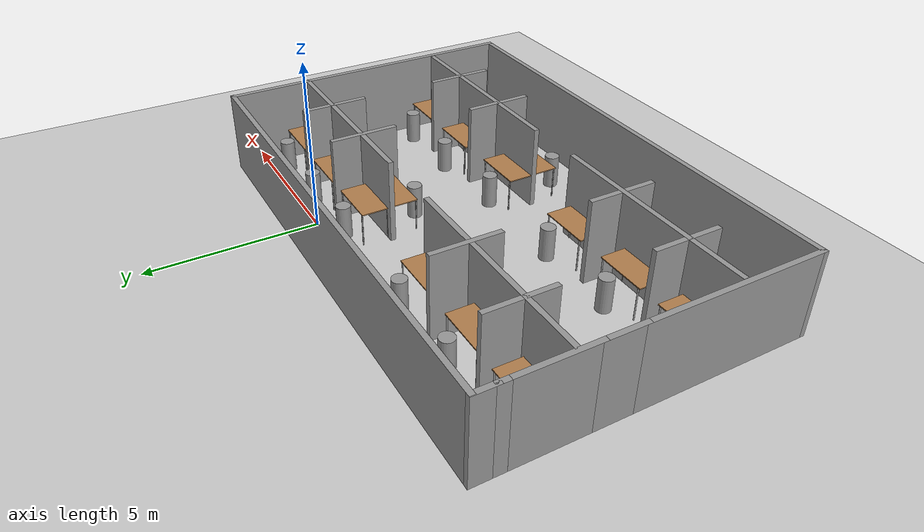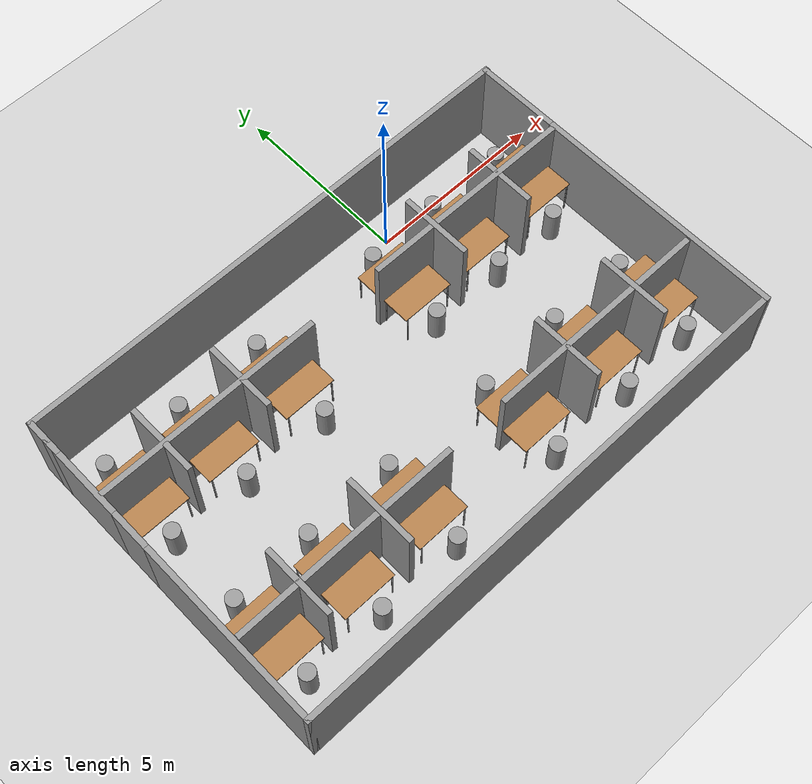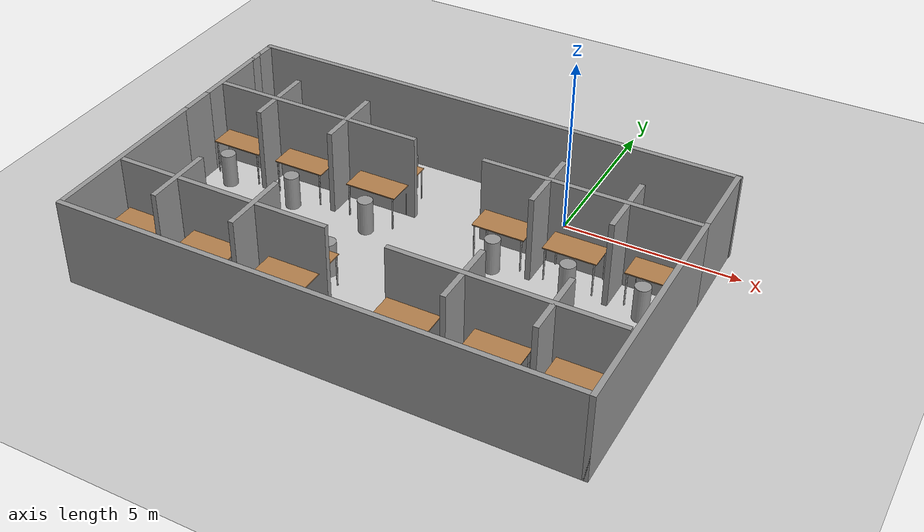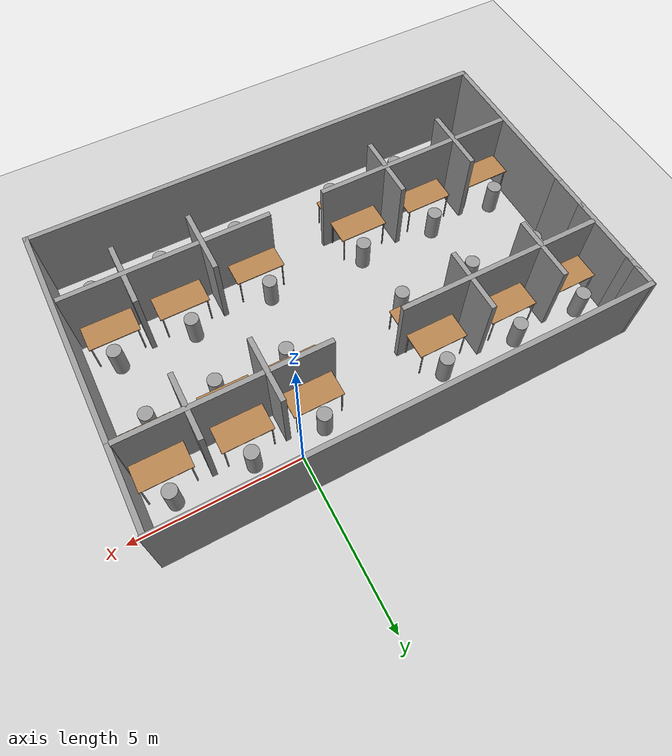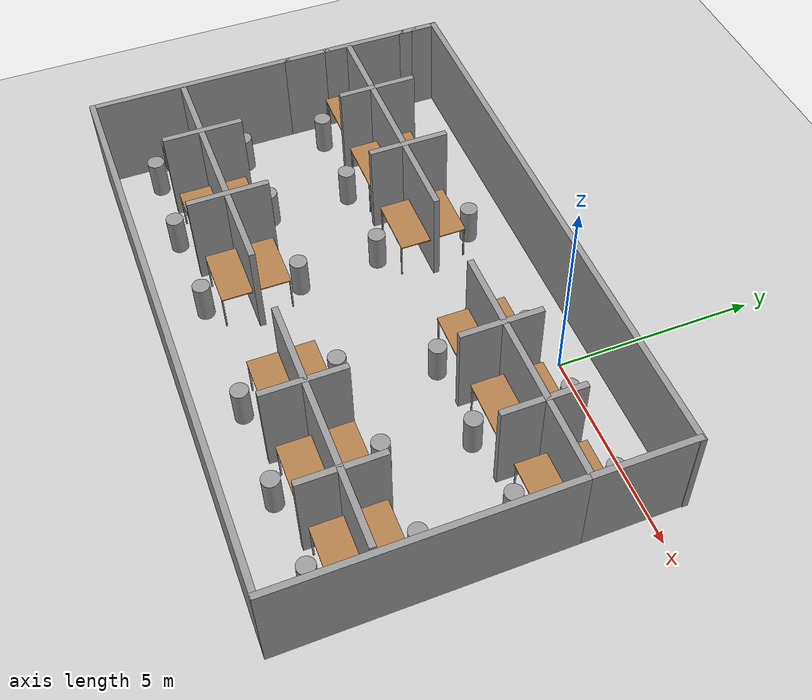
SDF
<sdf version="1.7">
 <world name="default">
  <scene><ambient>0.4 0.4 0.4 1</ambient><background>0.7 0.7 0.7 1</background><shadows>1</shadows></scene>
  <light name="sun" type="directional">
   <pose>0 0 10 0 -0 0</pose>
   <diffuse>0.8 0.8 0.8 1</diffuse>
   <specular>0.2 0.2 0.2 1</specular>
   <attenuation>
    <range>1000</range>
    <constant>0.9</constant>
    <linear>0.01</linear>
    <quadratic>0.001</quadratic>
   </attenuation>
   <direction>-0.5 0.1 -0.9</direction>
   <spot><inner_angle>0</inner_angle><outer_angle>0</outer_angle><falloff>0</falloff></spot>
  </light>
  <model name="ground_plane">
   <static>1</static>
   <link name="link">
    <collision name="collision">
     <geometry><plane><normal>0 0 1</normal><size>100 100</size></plane></geometry>
     <surface><friction><ode><mu>100</mu><mu2>50</mu2></ode></friction></surface>
    </collision>
    <visual name="visual">
     <cast_shadows>0</cast_shadows>
     <geometry><plane><normal>0 0 1</normal><size>100 100</size></plane></geometry>
     <material>
      <script><uri>file://media/materials/scripts/gazebo.material</uri><name>Gazebo/Grey</name></script>
     </material>
    </visual>
   </link>
  </model>
  <physics type="ode">
   <real_time_update_rate>0</real_time_update_rate>
   <max_step_size>0.001</max_step_size>
   <real_time_factor>1</real_time_factor>
   <ode>
    <solver>
     <type>quick</type>
     <iters>150</iters>
     <precon_iters>0</precon_iters>
     <sor>1.4</sor>
     <use_dynamic_moi_rescaling>1</use_dynamic_moi_rescaling>
    </solver>
    <constraints>
     <cfm>1e-05</cfm>
     <erp>0.2</erp>
     <contact_max_correcting_vel>2000</contact_max_correcting_vel>
     <contact_surface_layer>0.01</contact_surface_layer>
    </constraints>
   </ode>
  </physics>
  <gravity>0 0 -9.8</gravity>
  <magnetic_field>6e-06 2.3e-05 -4.2e-05</magnetic_field>
  <atmosphere type="adiabatic"/>
  <spherical_coordinates>
   <surface_model>EARTH_WGS84</surface_model>
   <latitude_deg>0</latitude_deg>
   <longitude_deg>0</longitude_deg>
   <elevation>0</elevation>
   <heading_deg>0</heading_deg>
  </spherical_coordinates>
  <model name="half_square">
   <pose>-2.87363 -3.76482 0 0 -0 0</pose>
   <link name="Wall_0">
    <collision name="Wall_0_Collision">
     <geometry><box><size>14.5 0.15 2.5</size></box></geometry>
     <pose>0 0 1.25 0 -0 0</pose>
    </collision>
    <visual name="Wall_0_Visual">
     <pose>0 0 1.25 0 -0 0</pose>
     <geometry><box><size>14.5 0.15 2.5</size></box></geometry>
     <material>
      <script><uri>file://media/materials/scripts/gazebo.material</uri><name>Gazebo/Grey</name></script>
      <ambient>1 1 1 1</ambient>
     </material>
     <meta><layer>0</layer></meta>
    </visual>
    <pose>-0.010056 -4.61503 0 0 -0 0</pose>
   </link>
   <link name="Wall_11">
    <collision name="Wall_11_Collision">
     <geometry><box><size>2.5 0.15 2.5</size></box></geometry>
     <pose>0 0 1.25 0 -0 0</pose>
    </collision>
    <visual name="Wall_11_Visual">
     <pose>0 0 1.25 0 -0 0</pose>
     <geometry><box><size>2.5 0.15 2.5</size></box></geometry>
     <material>
      <script><uri>file://media/materials/scripts/gazebo.material</uri><name>Gazebo/Grey</name></script>
      <ambient>1 1 1 1</ambient>
     </material>
     <meta><layer>0</layer></meta>
    </visual>
    <pose>7.16494 3.40997 0 0 -0 1.5708</pose>
   </link>
   <link name="Wall_13">
    <collision name="Wall_13_Collision">
     <geometry><box><size>0.730235 0.15 2.5</size></box></geometry>
     <pose>0 0 1.25 0 -0 0</pose>
    </collision>
    <visual name="Wall_13_Visual">
     <pose>0 0 1.25 0 -0 0</pose>
     <geometry><box><size>0.730235 0.15 2.5</size></box></geometry>
     <material>
      <script><uri>file://media/materials/scripts/gazebo.material</uri><name>Gazebo/Grey</name></script>
      <ambient>1 1 1 1</ambient>
     </material>
     <meta><layer>0</layer></meta>
    </visual>
    <pose>-7.18506 4.32491 0 0 -0 1.5708</pose>
   </link>
   <link name="Wall_14">
    <collision name="Wall_14_Collision">
     <geometry><box><size>14.5 0.15 2.5</size></box></geometry>
     <pose>0 0 1.25 0 -0 0</pose>
    </collision>
    <visual name="Wall_14_Visual">
     <pose>0 0 1.25 0 -0 0</pose>
     <geometry><box><size>14.5 0.15 2.5</size></box></geometry>
     <material>
      <script><uri>file://media/materials/scripts/gazebo.material</uri><name>Gazebo/Grey</name></script>
      <ambient>1 1 1 1</ambient>
     </material>
     <meta><layer>0</layer></meta>
    </visual>
    <pose>0.010057 4.61486 0 0 -0 0</pose>
   </link>
   <link name="Wall_2">
    <collision name="Wall_2_Collision">
     <geometry><box><size>5.25 0.15 2.5</size></box></geometry>
     <pose>0 0 1.25 0 -0 0</pose>
    </collision>
    <visual name="Wall_2_Visual">
     <pose>0 0 1.25 0 -0 0</pose>
     <geometry><box><size>5.25 0.15 2.5</size></box></geometry>
     <material>
      <script><uri>file://media/materials/scripts/gazebo.material</uri><name>Gazebo/Grey</name></script>
      <ambient>1 1 1 1</ambient>
     </material>
     <meta><layer>0</layer></meta>
    </visual>
    <pose>-7.18506 -2.06503 0 0 -0 1.5708</pose>
   </link>
   <link name="Wall_4">
    <collision name="Wall_4_Collision">
     <geometry><box><size>7 0.15 2.5</size></box></geometry>
     <pose>0 0 1.25 0 -0 0</pose>
    </collision>
    <visual name="Wall_4_Visual">
     <pose>0 0 1.25 0 -0 0</pose>
     <geometry><box><size>7 0.15 2.5</size></box></geometry>
     <material>
      <script><uri>file://media/materials/scripts/gazebo.material</uri><name>Gazebo/Grey</name></script>
      <ambient>1 1 1 1</ambient>
     </material>
     <meta><layer>0</layer></meta>
    </visual>
    <pose>7.16494 -1.19003 0 0 -0 1.5708</pose>
   </link>
   <link name="Wall_6">
    <collision name="Wall_6_Collision">
     <geometry><box><size>1.25 0.15 2.5</size></box></geometry>
     <pose>0 0 1.25 0 -0 0</pose>
    </collision>
    <visual name="Wall_6_Visual">
     <pose>0 0 1.25 0 -0 0</pose>
     <geometry><box><size>1.25 0.15 2.5</size></box></geometry>
     <material>
      <script><uri>file://media/materials/scripts/gazebo.material</uri><name>Gazebo/Grey</name></script>
      <ambient>1 1 1 1</ambient>
     </material>
     <meta><layer>0</layer></meta>
    </visual>
    <pose>-7.18506 1.03497 0 0 -0 1.5708</pose>
   </link>
   <link name="Wall_8">
    <collision name="Wall_8_Collision">
     <geometry><box><size>2.25 0.15 2.5</size></box></geometry>
     <pose>0 0 1.25 0 -0 0</pose>
    </collision>
    <visual name="Wall_8_Visual">
     <pose>0 0 1.25 0 -0 0</pose>
     <geometry><box><size>2.25 0.15 2.5</size></box></geometry>
     <material>
      <script><uri>file://media/materials/scripts/gazebo.material</uri><name>Gazebo/Grey</name></script>
      <ambient>1 1 1 1</ambient>
     </material>
     <meta><layer>0</layer></meta>
    </visual>
    <pose>-7.18506 2.63497 0 0 -0 1.5708</pose>
   </link>
   <link name="Wall_9">
    <collision name="Wall_9_Collision">
     <geometry><box><size>0.5 0.15 2.5</size></box></geometry>
     <pose>0 0 1.25 0 -0 0</pose>
    </collision>
    <visual name="Wall_9_Visual">
     <pose>0 0 1.25 0 -0 0</pose>
     <geometry><box><size>0.5 0.15 2.5</size></box></geometry>
     <material>
      <script><uri>file://media/materials/scripts/gazebo.material</uri><name>Gazebo/Grey</name></script>
      <ambient>1 1 1 1</ambient>
     </material>
     <meta><layer>0</layer></meta>
    </visual>
    <pose>-7.18506 3.85997 0 0 -0 1.5708</pose>
   </link>
   <static>1</static>
  </model>
  <plugin name="gazebo_occupancy_map" filename="libgazebo_2Dmap_plugin.so">
   <map_resolution>0.02</map_resolution>
   <map_height>0.7</map_height>
   <map_size_x>20</map_size_x>
   <map_size_y>20</map_size_y>
   <init_robot_x>0</init_robot_x>
   <init_robot_y>0</init_robot_y>
  </plugin>
  <model name="cubicle_walls">
   <pose>-2.89093 -3.53337 0 0 -0 0</pose>
   <link name="Wall_23">
    <collision name="Wall_23_Collision">
     <geometry><box><size>6 0.15 2.5</size></box></geometry>
     <pose>0 0 1.25 0 -0 0</pose>
    </collision>
    <visual name="Wall_23_Visual">
     <pose>0 0 1.25 0 -0 0</pose>
     <geometry><box><size>6 0.15 2.5</size></box></geometry>
     <material>
      <script><uri>file://media/materials/scripts/gazebo.material</uri><name>Gazebo/Grey</name></script>
      <ambient>1 1 1 1</ambient>
     </material>
     <meta><layer>0</layer></meta>
    </visual>
    <pose>4.1274 1.95737 0 0 -0 0</pose>
   </link>
   <link name="Wall_25">
    <collision name="Wall_25_Collision">
     <geometry><box><size>6.25 0.15 2.5</size></box></geometry>
     <pose>0 0 1.25 0 -0 0</pose>
    </collision>
    <visual name="Wall_25_Visual">
     <pose>0 0 1.25 0 -0 0</pose>
     <geometry><box><size>6.25 0.15 2.5</size></box></geometry>
     <material>
      <script><uri>file://media/materials/scripts/gazebo.material</uri><name>Gazebo/Grey</name></script>
      <ambient>1 1 1 1</ambient>
     </material>
     <meta><layer>0</layer></meta>
    </visual>
    <pose>3.94688 -2.51492 0 0 -0 0</pose>
   </link>
   <link name="Wall_27">
    <collision name="Wall_27_Collision">
     <geometry><box><size>6.25 0.15 2.5</size></box></geometry>
     <pose>0 0 1.25 0 -0 0</pose>
    </collision>
    <visual name="Wall_27_Visual">
     <pose>0 0 1.25 0 -0 0</pose>
     <geometry><box><size>6.25 0.15 2.5</size></box></geometry>
     <material>
      <script><uri>file://media/materials/scripts/gazebo.material</uri><name>Gazebo/Grey</name></script>
      <ambient>1 1 1 1</ambient>
     </material>
     <meta><layer>0</layer></meta>
    </visual>
    <pose>-3.9582 -2.5354 0 0 -0 3.14159</pose>
   </link>
   <link name="Wall_29">
    <collision name="Wall_29_Collision">
     <geometry><box><size>6.25 0.15 2.5</size></box></geometry>
     <pose>0 0 1.25 0 -0 0</pose>
    </collision>
    <visual name="Wall_29_Visual">
     <pose>0 0 1.25 0 -0 0</pose>
     <geometry><box><size>6.25 0.15 2.5</size></box></geometry>
     <material>
      <script><uri>file://media/materials/scripts/gazebo.material</uri><name>Gazebo/Grey</name></script>
      <ambient>1 1 1 1</ambient>
     </material>
     <meta><layer>0</layer></meta>
    </visual>
    <pose>-4.0024 1.95695 0 0 -0 3.14159</pose>
   </link>
   <link name="Wall_32">
    <collision name="Wall_32_Collision">
     <geometry><box><size>2 0.15 2.5</size></box></geometry>
     <pose>0 0 1.25 0 -0 0</pose>
    </collision>
    <visual name="Wall_32_Visual">
     <pose>0 0 1.25 0 -0 0</pose>
     <geometry><box><size>2 0.15 2.5</size></box></geometry>
     <material>
      <script><uri>file://media/materials/scripts/gazebo.material</uri><name>Gazebo/Grey</name></script>
      <ambient>1 1 1 1</ambient>
     </material>
     <meta><layer>0</layer></meta>
    </visual>
    <pose>5.20289 -2.49121 0 0 -0 -1.5708</pose>
   </link>
   <link name="Wall_34">
    <collision name="Wall_34_Collision">
     <geometry><box><size>2 0.15 2.5</size></box></geometry>
     <pose>0 0 1.25 0 -0 0</pose>
    </collision>
    <visual name="Wall_34_Visual">
     <pose>0 0 1.25 0 -0 0</pose>
     <geometry><box><size>2 0.15 2.5</size></box></geometry>
     <material>
      <script><uri>file://media/materials/scripts/gazebo.material</uri><name>Gazebo/Grey</name></script>
      <ambient>1 1 1 1</ambient>
     </material>
     <meta><layer>0</layer></meta>
    </visual>
    <pose>2.90891 -2.53337 0 0 -0 -1.5708</pose>
   </link>
   <link name="Wall_36">
    <collision name="Wall_36_Collision">
     <geometry><box><size>2 0.15 2.5</size></box></geometry>
     <pose>0 0 1.25 0 -0 0</pose>
    </collision>
    <visual name="Wall_36_Visual">
     <pose>0 0 1.25 0 -0 0</pose>
     <geometry><box><size>2 0.15 2.5</size></box></geometry>
     <material>
      <script><uri>file://media/materials/scripts/gazebo.material</uri><name>Gazebo/Grey</name></script>
      <ambient>1 1 1 1</ambient>
     </material>
     <meta><layer>0</layer></meta>
    </visual>
    <pose>5.17332 1.88452 0 0 -0 1.5708</pose>
   </link>
   <link name="Wall_40">
    <collision name="Wall_40_Collision">
     <geometry><box><size>2 0.15 2.5</size></box></geometry>
     <pose>0 0 1.25 0 -0 0</pose>
    </collision>
    <visual name="Wall_40_Visual">
     <pose>0 0 1.25 0 -0 0</pose>
     <geometry><box><size>2 0.15 2.5</size></box></geometry>
     <material>
      <script><uri>file://media/materials/scripts/gazebo.material</uri><name>Gazebo/Grey</name></script>
      <ambient>1 1 1 1</ambient>
     </material>
     <meta><layer>0</layer></meta>
    </visual>
    <pose>3.01751 1.89009 0 0 -0 1.5708</pose>
   </link>
   <link name="Wall_42">
    <collision name="Wall_42_Collision">
     <geometry><box><size>2 0.15 2.5</size></box></geometry>
     <pose>0 0 1.25 0 -0 0</pose>
    </collision>
    <visual name="Wall_42_Visual">
     <pose>0 0 1.25 0 -0 0</pose>
     <geometry><box><size>2 0.15 2.5</size></box></geometry>
     <material>
      <script><uri>file://media/materials/scripts/gazebo.material</uri><name>Gazebo/Grey</name></script>
      <ambient>1 1 1 1</ambient>
     </material>
     <meta><layer>0</layer></meta>
    </visual>
    <pose>-3.01912 2.06337 0 0 -0 -1.5708</pose>
   </link>
   <link name="Wall_44">
    <collision name="Wall_44_Collision">
     <geometry><box><size>2 0.15 2.5</size></box></geometry>
     <pose>0 0 1.25 0 -0 0</pose>
    </collision>
    <visual name="Wall_44_Visual">
     <pose>0 0 1.25 0 -0 0</pose>
     <geometry><box><size>2 0.15 2.5</size></box></geometry>
     <material>
      <script><uri>file://media/materials/scripts/gazebo.material</uri><name>Gazebo/Grey</name></script>
      <ambient>1 1 1 1</ambient>
     </material>
     <meta><layer>0</layer></meta>
    </visual>
    <pose>-5.31032 2.08086 0 0 -0 -1.5708</pose>
   </link>
   <link name="Wall_46">
    <collision name="Wall_46_Collision">
     <geometry><box><size>2 0.15 2.5</size></box></geometry>
     <pose>0 0 1.25 0 -0 0</pose>
    </collision>
    <visual name="Wall_46_Visual">
     <pose>0 0 1.25 0 -0 0</pose>
     <geometry><box><size>2 0.15 2.5</size></box></geometry>
     <material>
      <script><uri>file://media/materials/scripts/gazebo.material</uri><name>Gazebo/Grey</name></script>
      <ambient>1 1 1 1</ambient>
     </material>
     <meta><layer>0</layer></meta>
    </visual>
    <pose>-2.96649 -2.51109 0 0 -0 -1.5708</pose>
   </link>
   <link name="Wall_48">
    <collision name="Wall_48_Collision">
     <geometry><box><size>2 0.15 2.5</size></box></geometry>
     <pose>0 0 1.25 0 -0 0</pose>
    </collision>
    <visual name="Wall_48_Visual">
     <pose>0 0 1.25 0 -0 0</pose>
     <geometry><box><size>2 0.15 2.5</size></box></geometry>
     <material>
      <script><uri>file://media/materials/scripts/gazebo.material</uri><name>Gazebo/Grey</name></script>
      <ambient>1 1 1 1</ambient>
     </material>
     <meta><layer>0</layer></meta>
    </visual>
    <pose>-5.32952 -2.50161 0 0 -0 -1.5708</pose>
   </link>
   <static>1</static>
  </model>
  <model name="table">
   <static>1</static>
   <link name="link">
    <collision name="surface">
     <pose>0 0 1 0 -0 0</pose>
     <geometry><box><size>1.5 0.8 0.03</size></box></geometry>
     <surface><friction><ode><mu>0.6</mu><mu2>0.6</mu2></ode></friction></surface>
    </collision>
    <visual name="visual1">
     <pose>0 0 1 0 -0 0</pose>
     <geometry><box><size>1.5 0.8 0.03</size></box></geometry>
     <material>
      <script><uri>file://media/materials/scripts/gazebo.material</uri><name>Gazebo/Wood</name></script>
     </material>
    </visual>
    <collision name="front_left_leg">
     <pose>0.68 0.38 0.5 0 -0 0</pose>
     <geometry><cylinder><radius>0.02</radius><length>1</length></cylinder></geometry>
    </collision>
    <visual name="front_left_leg">
     <pose>0.68 0.38 0.5 0 -0 0</pose>
     <geometry><cylinder><radius>0.02</radius><length>1</length></cylinder></geometry>
     <material>
      <script><uri>file://media/materials/scripts/gazebo.material</uri><name>Gazebo/Grey</name></script>
     </material>
    </visual>
    <collision name="front_right_leg">
     <pose>0.68 -0.38 0.5 0 -0 0</pose>
     <geometry><cylinder><radius>0.02</radius><length>1</length></cylinder></geometry>
    </collision>
    <visual name="front_right_leg">
     <pose>0.68 -0.38 0.5 0 -0 0</pose>
     <geometry><cylinder><radius>0.02</radius><length>1</length></cylinder></geometry>
     <material>
      <script><uri>file://media/materials/scripts/gazebo.material</uri><name>Gazebo/Grey</name></script>
     </material>
    </visual>
    <collision name="back_right_leg">
     <pose>-0.68 -0.38 0.5 0 -0 0</pose>
     <geometry><cylinder><radius>0.02</radius><length>1</length></cylinder></geometry>
    </collision>
    <visual name="back_right_leg">
     <pose>-0.68 -0.38 0.5 0 -0 0</pose>
     <geometry><cylinder><radius>0.02</radius><length>1</length></cylinder></geometry>
     <material>
      <script><uri>file://media/materials/scripts/gazebo.material</uri><name>Gazebo/Grey</name></script>
     </material>
    </visual>
    <collision name="back_left_leg">
     <pose>-0.68 0.38 0.5 0 -0 0</pose>
     <geometry><cylinder><radius>0.02</radius><length>1</length></cylinder></geometry>
    </collision>
    <visual name="back_left_leg">
     <pose>-0.68 0.38 0.5 0 -0 0</pose>
     <geometry><cylinder><radius>0.02</radius><length>1</length></cylinder></geometry>
     <material>
      <script><uri>file://media/materials/scripts/gazebo.material</uri><name>Gazebo/Grey</name></script>
     </material>
    </visual>
   </link>
   <pose>1.18362 -1.10469 0 0 -0 0</pose>
  </model>
  <model name="table_0">
   <static>1</static>
   <link name="link">
    <collision name="surface">
     <pose>0 0 1 0 -0 0</pose>
     <geometry><box><size>1.5 0.8 0.03</size></box></geometry>
     <surface><friction><ode><mu>0.6</mu><mu2>0.6</mu2></ode></friction></surface>
    </collision>
    <visual name="visual1">
     <pose>0 0 1 0 -0 0</pose>
     <geometry><box><size>1.5 0.8 0.03</size></box></geometry>
     <material>
      <script><uri>file://media/materials/scripts/gazebo.material</uri><name>Gazebo/Wood</name></script>
     </material>
    </visual>
    <collision name="front_left_leg">
     <pose>0.68 0.38 0.5 0 -0 0</pose>
     <geometry><cylinder><radius>0.02</radius><length>1</length></cylinder></geometry>
    </collision>
    <visual name="front_left_leg">
     <pose>0.68 0.38 0.5 0 -0 0</pose>
     <geometry><cylinder><radius>0.02</radius><length>1</length></cylinder></geometry>
     <material>
      <script><uri>file://media/materials/scripts/gazebo.material</uri><name>Gazebo/Grey</name></script>
     </material>
    </visual>
    <collision name="front_right_leg">
     <pose>0.68 -0.38 0.5 0 -0 0</pose>
     <geometry><cylinder><radius>0.02</radius><length>1</length></cylinder></geometry>
    </collision>
    <visual name="front_right_leg">
     <pose>0.68 -0.38 0.5 0 -0 0</pose>
     <geometry><cylinder><radius>0.02</radius><length>1</length></cylinder></geometry>
     <material>
      <script><uri>file://media/materials/scripts/gazebo.material</uri><name>Gazebo/Grey</name></script>
     </material>
    </visual>
    <collision name="back_right_leg">
     <pose>-0.68 -0.38 0.5 0 -0 0</pose>
     <geometry><cylinder><radius>0.02</radius><length>1</length></cylinder></geometry>
    </collision>
    <visual name="back_right_leg">
     <pose>-0.68 -0.38 0.5 0 -0 0</pose>
     <geometry><cylinder><radius>0.02</radius><length>1</length></cylinder></geometry>
     <material>
      <script><uri>file://media/materials/scripts/gazebo.material</uri><name>Gazebo/Grey</name></script>
     </material>
    </visual>
    <collision name="back_left_leg">
     <pose>-0.68 0.38 0.5 0 -0 0</pose>
     <geometry><cylinder><radius>0.02</radius><length>1</length></cylinder></geometry>
    </collision>
    <visual name="back_left_leg">
     <pose>-0.68 0.38 0.5 0 -0 0</pose>
     <geometry><cylinder><radius>0.02</radius><length>1</length></cylinder></geometry>
     <material>
      <script><uri>file://media/materials/scripts/gazebo.material</uri><name>Gazebo/Grey</name></script>
     </material>
    </visual>
   </link>
   <pose>3.41773 -1.11914 0 0 -0 0</pose>
  </model>
  <model name="table_1">
   <static>1</static>
   <link name="link">
    <collision name="surface">
     <pose>0 0 1 0 -0 0</pose>
     <geometry><box><size>1.5 0.8 0.03</size></box></geometry>
     <surface><friction><ode><mu>0.6</mu><mu2>0.6</mu2></ode></friction></surface>
    </collision>
    <visual name="visual1">
     <pose>0 0 1 0 -0 0</pose>
     <geometry><box><size>1.5 0.8 0.03</size></box></geometry>
     <material>
      <script><uri>file://media/materials/scripts/gazebo.material</uri><name>Gazebo/Wood</name></script>
     </material>
    </visual>
    <collision name="front_left_leg">
     <pose>0.68 0.38 0.5 0 -0 0</pose>
     <geometry><cylinder><radius>0.02</radius><length>1</length></cylinder></geometry>
    </collision>
    <visual name="front_left_leg">
     <pose>0.68 0.38 0.5 0 -0 0</pose>
     <geometry><cylinder><radius>0.02</radius><length>1</length></cylinder></geometry>
     <material>
      <script><uri>file://media/materials/scripts/gazebo.material</uri><name>Gazebo/Grey</name></script>
     </material>
    </visual>
    <collision name="front_right_leg">
     <pose>0.68 -0.38 0.5 0 -0 0</pose>
     <geometry><cylinder><radius>0.02</radius><length>1</length></cylinder></geometry>
    </collision>
    <visual name="front_right_leg">
     <pose>0.68 -0.38 0.5 0 -0 0</pose>
     <geometry><cylinder><radius>0.02</radius><length>1</length></cylinder></geometry>
     <material>
      <script><uri>file://media/materials/scripts/gazebo.material</uri><name>Gazebo/Grey</name></script>
     </material>
    </visual>
    <collision name="back_right_leg">
     <pose>-0.68 -0.38 0.5 0 -0 0</pose>
     <geometry><cylinder><radius>0.02</radius><length>1</length></cylinder></geometry>
    </collision>
    <visual name="back_right_leg">
     <pose>-0.68 -0.38 0.5 0 -0 0</pose>
     <geometry><cylinder><radius>0.02</radius><length>1</length></cylinder></geometry>
     <material>
      <script><uri>file://media/materials/scripts/gazebo.material</uri><name>Gazebo/Grey</name></script>
     </material>
    </visual>
    <collision name="back_left_leg">
     <pose>-0.68 0.38 0.5 0 -0 0</pose>
     <geometry><cylinder><radius>0.02</radius><length>1</length></cylinder></geometry>
    </collision>
    <visual name="back_left_leg">
     <pose>-0.68 0.38 0.5 0 -0 0</pose>
     <geometry><cylinder><radius>0.02</radius><length>1</length></cylinder></geometry>
     <material>
      <script><uri>file://media/materials/scripts/gazebo.material</uri><name>Gazebo/Grey</name></script>
     </material>
    </visual>
   </link>
   <pose>3.39795 -2.01239 0 0 -0 0</pose>
  </model>
  <model name="table_2">
   <static>1</static>
   <link name="link">
    <collision name="surface">
     <pose>0 0 1 0 -0 0</pose>
     <geometry><box><size>1.5 0.8 0.03</size></box></geometry>
     <surface><friction><ode><mu>0.6</mu><mu2>0.6</mu2></ode></friction></surface>
    </collision>
    <visual name="visual1">
     <pose>0 0 1 0 -0 0</pose>
     <geometry><box><size>1.5 0.8 0.03</size></box></geometry>
     <material>
      <script><uri>file://media/materials/scripts/gazebo.material</uri><name>Gazebo/Wood</name></script>
     </material>
    </visual>
    <collision name="front_left_leg">
     <pose>0.68 0.38 0.5 0 -0 0</pose>
     <geometry><cylinder><radius>0.02</radius><length>1</length></cylinder></geometry>
    </collision>
    <visual name="front_left_leg">
     <pose>0.68 0.38 0.5 0 -0 0</pose>
     <geometry><cylinder><radius>0.02</radius><length>1</length></cylinder></geometry>
     <material>
      <script><uri>file://media/materials/scripts/gazebo.material</uri><name>Gazebo/Grey</name></script>
     </material>
    </visual>
    <collision name="front_right_leg">
     <pose>0.68 -0.38 0.5 0 -0 0</pose>
     <geometry><cylinder><radius>0.02</radius><length>1</length></cylinder></geometry>
    </collision>
    <visual name="front_right_leg">
     <pose>0.68 -0.38 0.5 0 -0 0</pose>
     <geometry><cylinder><radius>0.02</radius><length>1</length></cylinder></geometry>
     <material>
      <script><uri>file://media/materials/scripts/gazebo.material</uri><name>Gazebo/Grey</name></script>
     </material>
    </visual>
    <collision name="back_right_leg">
     <pose>-0.68 -0.38 0.5 0 -0 0</pose>
     <geometry><cylinder><radius>0.02</radius><length>1</length></cylinder></geometry>
    </collision>
    <visual name="back_right_leg">
     <pose>-0.68 -0.38 0.5 0 -0 0</pose>
     <geometry><cylinder><radius>0.02</radius><length>1</length></cylinder></geometry>
     <material>
      <script><uri>file://media/materials/scripts/gazebo.material</uri><name>Gazebo/Grey</name></script>
     </material>
    </visual>
    <collision name="back_left_leg">
     <pose>-0.68 0.38 0.5 0 -0 0</pose>
     <geometry><cylinder><radius>0.02</radius><length>1</length></cylinder></geometry>
    </collision>
    <visual name="back_left_leg">
     <pose>-0.68 0.38 0.5 0 -0 0</pose>
     <geometry><cylinder><radius>0.02</radius><length>1</length></cylinder></geometry>
     <material>
      <script><uri>file://media/materials/scripts/gazebo.material</uri><name>Gazebo/Grey</name></script>
     </material>
    </visual>
   </link>
   <pose>1.17009 -2.05921 0 0 -0 0</pose>
  </model>
  <model name="table_3">
   <static>1</static>
   <link name="link">
    <collision name="surface">
     <pose>0 0 1 0 -0 0</pose>
     <geometry><box><size>1.5 0.8 0.03</size></box></geometry>
     <surface><friction><ode><mu>0.6</mu><mu2>0.6</mu2></ode></friction></surface>
    </collision>
    <visual name="visual1">
     <pose>0 0 1 0 -0 0</pose>
     <geometry><box><size>1.5 0.8 0.03</size></box></geometry>
     <material>
      <script><uri>file://media/materials/scripts/gazebo.material</uri><name>Gazebo/Wood</name></script>
     </material>
    </visual>
    <collision name="front_left_leg">
     <pose>0.68 0.38 0.5 0 -0 0</pose>
     <geometry><cylinder><radius>0.02</radius><length>1</length></cylinder></geometry>
    </collision>
    <visual name="front_left_leg">
     <pose>0.68 0.38 0.5 0 -0 0</pose>
     <geometry><cylinder><radius>0.02</radius><length>1</length></cylinder></geometry>
     <material>
      <script><uri>file://media/materials/scripts/gazebo.material</uri><name>Gazebo/Grey</name></script>
     </material>
    </visual>
    <collision name="front_right_leg">
     <pose>0.68 -0.38 0.5 0 -0 0</pose>
     <geometry><cylinder><radius>0.02</radius><length>1</length></cylinder></geometry>
    </collision>
    <visual name="front_right_leg">
     <pose>0.68 -0.38 0.5 0 -0 0</pose>
     <geometry><cylinder><radius>0.02</radius><length>1</length></cylinder></geometry>
     <material>
      <script><uri>file://media/materials/scripts/gazebo.material</uri><name>Gazebo/Grey</name></script>
     </material>
    </visual>
    <collision name="back_right_leg">
     <pose>-0.68 -0.38 0.5 0 -0 0</pose>
     <geometry><cylinder><radius>0.02</radius><length>1</length></cylinder></geometry>
    </collision>
    <visual name="back_right_leg">
     <pose>-0.68 -0.38 0.5 0 -0 0</pose>
     <geometry><cylinder><radius>0.02</radius><length>1</length></cylinder></geometry>
     <material>
      <script><uri>file://media/materials/scripts/gazebo.material</uri><name>Gazebo/Grey</name></script>
     </material>
    </visual>
    <collision name="back_left_leg">
     <pose>-0.68 0.38 0.5 0 -0 0</pose>
     <geometry><cylinder><radius>0.02</radius><length>1</length></cylinder></geometry>
    </collision>
    <visual name="back_left_leg">
     <pose>-0.68 0.38 0.5 0 -0 0</pose>
     <geometry><cylinder><radius>0.02</radius><length>1</length></cylinder></geometry>
     <material>
      <script><uri>file://media/materials/scripts/gazebo.material</uri><name>Gazebo/Grey</name></script>
     </material>
    </visual>
   </link>
   <pose>-0.867477 -2.03442 0 0 -0 0</pose>
  </model>
  <model name="table_4">
   <static>1</static>
   <link name="link">
    <collision name="surface">
     <pose>0 0 1 0 -0 0</pose>
     <geometry><box><size>1.5 0.8 0.03</size></box></geometry>
     <surface><friction><ode><mu>0.6</mu><mu2>0.6</mu2></ode></friction></surface>
    </collision>
    <visual name="visual1">
     <pose>0 0 1 0 -0 0</pose>
     <geometry><box><size>1.5 0.8 0.03</size></box></geometry>
     <material>
      <script><uri>file://media/materials/scripts/gazebo.material</uri><name>Gazebo/Wood</name></script>
     </material>
    </visual>
    <collision name="front_left_leg">
     <pose>0.68 0.38 0.5 0 -0 0</pose>
     <geometry><cylinder><radius>0.02</radius><length>1</length></cylinder></geometry>
    </collision>
    <visual name="front_left_leg">
     <pose>0.68 0.38 0.5 0 -0 0</pose>
     <geometry><cylinder><radius>0.02</radius><length>1</length></cylinder></geometry>
     <material>
      <script><uri>file://media/materials/scripts/gazebo.material</uri><name>Gazebo/Grey</name></script>
     </material>
    </visual>
    <collision name="front_right_leg">
     <pose>0.68 -0.38 0.5 0 -0 0</pose>
     <geometry><cylinder><radius>0.02</radius><length>1</length></cylinder></geometry>
    </collision>
    <visual name="front_right_leg">
     <pose>0.68 -0.38 0.5 0 -0 0</pose>
     <geometry><cylinder><radius>0.02</radius><length>1</length></cylinder></geometry>
     <material>
      <script><uri>file://media/materials/scripts/gazebo.material</uri><name>Gazebo/Grey</name></script>
     </material>
    </visual>
    <collision name="back_right_leg">
     <pose>-0.68 -0.38 0.5 0 -0 0</pose>
     <geometry><cylinder><radius>0.02</radius><length>1</length></cylinder></geometry>
    </collision>
    <visual name="back_right_leg">
     <pose>-0.68 -0.38 0.5 0 -0 0</pose>
     <geometry><cylinder><radius>0.02</radius><length>1</length></cylinder></geometry>
     <material>
      <script><uri>file://media/materials/scripts/gazebo.material</uri><name>Gazebo/Grey</name></script>
     </material>
    </visual>
    <collision name="back_left_leg">
     <pose>-0.68 0.38 0.5 0 -0 0</pose>
     <geometry><cylinder><radius>0.02</radius><length>1</length></cylinder></geometry>
    </collision>
    <visual name="back_left_leg">
     <pose>-0.68 0.38 0.5 0 -0 0</pose>
     <geometry><cylinder><radius>0.02</radius><length>1</length></cylinder></geometry>
     <material>
      <script><uri>file://media/materials/scripts/gazebo.material</uri><name>Gazebo/Grey</name></script>
     </material>
    </visual>
   </link>
   <pose>-0.882753 -1.12704 0 0 -0 0</pose>
  </model>
  <model name="table_5">
   <static>1</static>
   <link name="link">
    <collision name="surface">
     <pose>0 0 1 0 -0 0</pose>
     <geometry><box><size>1.5 0.8 0.03</size></box></geometry>
     <surface><friction><ode><mu>0.6</mu><mu2>0.6</mu2></ode></friction></surface>
    </collision>
    <visual name="visual1">
     <pose>0 0 1 0 -0 0</pose>
     <geometry><box><size>1.5 0.8 0.03</size></box></geometry>
     <material>
      <script><uri>file://media/materials/scripts/gazebo.material</uri><name>Gazebo/Wood</name></script>
     </material>
    </visual>
    <collision name="front_left_leg">
     <pose>0.68 0.38 0.5 0 -0 0</pose>
     <geometry><cylinder><radius>0.02</radius><length>1</length></cylinder></geometry>
    </collision>
    <visual name="front_left_leg">
     <pose>0.68 0.38 0.5 0 -0 0</pose>
     <geometry><cylinder><radius>0.02</radius><length>1</length></cylinder></geometry>
     <material>
      <script><uri>file://media/materials/scripts/gazebo.material</uri><name>Gazebo/Grey</name></script>
     </material>
    </visual>
    <collision name="front_right_leg">
     <pose>0.68 -0.38 0.5 0 -0 0</pose>
     <geometry><cylinder><radius>0.02</radius><length>1</length></cylinder></geometry>
    </collision>
    <visual name="front_right_leg">
     <pose>0.68 -0.38 0.5 0 -0 0</pose>
     <geometry><cylinder><radius>0.02</radius><length>1</length></cylinder></geometry>
     <material>
      <script><uri>file://media/materials/scripts/gazebo.material</uri><name>Gazebo/Grey</name></script>
     </material>
    </visual>
    <collision name="back_right_leg">
     <pose>-0.68 -0.38 0.5 0 -0 0</pose>
     <geometry><cylinder><radius>0.02</radius><length>1</length></cylinder></geometry>
    </collision>
    <visual name="back_right_leg">
     <pose>-0.68 -0.38 0.5 0 -0 0</pose>
     <geometry><cylinder><radius>0.02</radius><length>1</length></cylinder></geometry>
     <material>
      <script><uri>file://media/materials/scripts/gazebo.material</uri><name>Gazebo/Grey</name></script>
     </material>
    </visual>
    <collision name="back_left_leg">
     <pose>-0.68 0.38 0.5 0 -0 0</pose>
     <geometry><cylinder><radius>0.02</radius><length>1</length></cylinder></geometry>
    </collision>
    <visual name="back_left_leg">
     <pose>-0.68 0.38 0.5 0 -0 0</pose>
     <geometry><cylinder><radius>0.02</radius><length>1</length></cylinder></geometry>
     <material>
      <script><uri>file://media/materials/scripts/gazebo.material</uri><name>Gazebo/Grey</name></script>
     </material>
    </visual>
   </link>
   <pose>3.22024 -5.55279 0 0 -0 0</pose>
  </model>
  <model name="table_6">
   <static>1</static>
   <link name="link">
    <collision name="surface">
     <pose>0 0 1 0 -0 0</pose>
     <geometry><box><size>1.5 0.8 0.03</size></box></geometry>
     <surface><friction><ode><mu>0.6</mu><mu2>0.6</mu2></ode></friction></surface>
    </collision>
    <visual name="visual1">
     <pose>0 0 1 0 -0 0</pose>
     <geometry><box><size>1.5 0.8 0.03</size></box></geometry>
     <material>
      <script><uri>file://media/materials/scripts/gazebo.material</uri><name>Gazebo/Wood</name></script>
     </material>
    </visual>
    <collision name="front_left_leg">
     <pose>0.68 0.38 0.5 0 -0 0</pose>
     <geometry><cylinder><radius>0.02</radius><length>1</length></cylinder></geometry>
    </collision>
    <visual name="front_left_leg">
     <pose>0.68 0.38 0.5 0 -0 0</pose>
     <geometry><cylinder><radius>0.02</radius><length>1</length></cylinder></geometry>
     <material>
      <script><uri>file://media/materials/scripts/gazebo.material</uri><name>Gazebo/Grey</name></script>
     </material>
    </visual>
    <collision name="front_right_leg">
     <pose>0.68 -0.38 0.5 0 -0 0</pose>
     <geometry><cylinder><radius>0.02</radius><length>1</length></cylinder></geometry>
    </collision>
    <visual name="front_right_leg">
     <pose>0.68 -0.38 0.5 0 -0 0</pose>
     <geometry><cylinder><radius>0.02</radius><length>1</length></cylinder></geometry>
     <material>
      <script><uri>file://media/materials/scripts/gazebo.material</uri><name>Gazebo/Grey</name></script>
     </material>
    </visual>
    <collision name="back_right_leg">
     <pose>-0.68 -0.38 0.5 0 -0 0</pose>
     <geometry><cylinder><radius>0.02</radius><length>1</length></cylinder></geometry>
    </collision>
    <visual name="back_right_leg">
     <pose>-0.68 -0.38 0.5 0 -0 0</pose>
     <geometry><cylinder><radius>0.02</radius><length>1</length></cylinder></geometry>
     <material>
      <script><uri>file://media/materials/scripts/gazebo.material</uri><name>Gazebo/Grey</name></script>
     </material>
    </visual>
    <collision name="back_left_leg">
     <pose>-0.68 0.38 0.5 0 -0 0</pose>
     <geometry><cylinder><radius>0.02</radius><length>1</length></cylinder></geometry>
    </collision>
    <visual name="back_left_leg">
     <pose>-0.68 0.38 0.5 0 -0 0</pose>
     <geometry><cylinder><radius>0.02</radius><length>1</length></cylinder></geometry>
     <material>
      <script><uri>file://media/materials/scripts/gazebo.material</uri><name>Gazebo/Grey</name></script>
     </material>
    </visual>
   </link>
   <pose>1.12922 -5.55077 0 0 -0 0</pose>
  </model>
  <model name="table_7">
   <static>1</static>
   <link name="link">
    <collision name="surface">
     <pose>0 0 1 0 -0 0</pose>
     <geometry><box><size>1.5 0.8 0.03</size></box></geometry>
     <surface><friction><ode><mu>0.6</mu><mu2>0.6</mu2></ode></friction></surface>
    </collision>
    <visual name="visual1">
     <pose>0 0 1 0 -0 0</pose>
     <geometry><box><size>1.5 0.8 0.03</size></box></geometry>
     <material>
      <script><uri>file://media/materials/scripts/gazebo.material</uri><name>Gazebo/Wood</name></script>
     </material>
    </visual>
    <collision name="front_left_leg">
     <pose>0.68 0.38 0.5 0 -0 0</pose>
     <geometry><cylinder><radius>0.02</radius><length>1</length></cylinder></geometry>
    </collision>
    <visual name="front_left_leg">
     <pose>0.68 0.38 0.5 0 -0 0</pose>
     <geometry><cylinder><radius>0.02</radius><length>1</length></cylinder></geometry>
     <material>
      <script><uri>file://media/materials/scripts/gazebo.material</uri><name>Gazebo/Grey</name></script>
     </material>
    </visual>
    <collision name="front_right_leg">
     <pose>0.68 -0.38 0.5 0 -0 0</pose>
     <geometry><cylinder><radius>0.02</radius><length>1</length></cylinder></geometry>
    </collision>
    <visual name="front_right_leg">
     <pose>0.68 -0.38 0.5 0 -0 0</pose>
     <geometry><cylinder><radius>0.02</radius><length>1</length></cylinder></geometry>
     <material>
      <script><uri>file://media/materials/scripts/gazebo.material</uri><name>Gazebo/Grey</name></script>
     </material>
    </visual>
    <collision name="back_right_leg">
     <pose>-0.68 -0.38 0.5 0 -0 0</pose>
     <geometry><cylinder><radius>0.02</radius><length>1</length></cylinder></geometry>
    </collision>
    <visual name="back_right_leg">
     <pose>-0.68 -0.38 0.5 0 -0 0</pose>
     <geometry><cylinder><radius>0.02</radius><length>1</length></cylinder></geometry>
     <material>
      <script><uri>file://media/materials/scripts/gazebo.material</uri><name>Gazebo/Grey</name></script>
     </material>
    </visual>
    <collision name="back_left_leg">
     <pose>-0.68 0.38 0.5 0 -0 0</pose>
     <geometry><cylinder><radius>0.02</radius><length>1</length></cylinder></geometry>
    </collision>
    <visual name="back_left_leg">
     <pose>-0.68 0.38 0.5 0 -0 0</pose>
     <geometry><cylinder><radius>0.02</radius><length>1</length></cylinder></geometry>
     <material>
      <script><uri>file://media/materials/scripts/gazebo.material</uri><name>Gazebo/Grey</name></script>
     </material>
    </visual>
   </link>
   <pose>-1.2949 -5.65253 0 0 -0 0</pose>
  </model>
  <model name="table_8">
   <static>1</static>
   <link name="link">
    <collision name="surface">
     <pose>0 0 1 0 -0 0</pose>
     <geometry><box><size>1.5 0.8 0.03</size></box></geometry>
     <surface><friction><ode><mu>0.6</mu><mu2>0.6</mu2></ode></friction></surface>
    </collision>
    <visual name="visual1">
     <pose>0 0 1 0 -0 0</pose>
     <geometry><box><size>1.5 0.8 0.03</size></box></geometry>
     <material>
      <script><uri>file://media/materials/scripts/gazebo.material</uri><name>Gazebo/Wood</name></script>
     </material>
    </visual>
    <collision name="front_left_leg">
     <pose>0.68 0.38 0.5 0 -0 0</pose>
     <geometry><cylinder><radius>0.02</radius><length>1</length></cylinder></geometry>
    </collision>
    <visual name="front_left_leg">
     <pose>0.68 0.38 0.5 0 -0 0</pose>
     <geometry><cylinder><radius>0.02</radius><length>1</length></cylinder></geometry>
     <material>
      <script><uri>file://media/materials/scripts/gazebo.material</uri><name>Gazebo/Grey</name></script>
     </material>
    </visual>
    <collision name="front_right_leg">
     <pose>0.68 -0.38 0.5 0 -0 0</pose>
     <geometry><cylinder><radius>0.02</radius><length>1</length></cylinder></geometry>
    </collision>
    <visual name="front_right_leg">
     <pose>0.68 -0.38 0.5 0 -0 0</pose>
     <geometry><cylinder><radius>0.02</radius><length>1</length></cylinder></geometry>
     <material>
      <script><uri>file://media/materials/scripts/gazebo.material</uri><name>Gazebo/Grey</name></script>
     </material>
    </visual>
    <collision name="back_right_leg">
     <pose>-0.68 -0.38 0.5 0 -0 0</pose>
     <geometry><cylinder><radius>0.02</radius><length>1</length></cylinder></geometry>
    </collision>
    <visual name="back_right_leg">
     <pose>-0.68 -0.38 0.5 0 -0 0</pose>
     <geometry><cylinder><radius>0.02</radius><length>1</length></cylinder></geometry>
     <material>
      <script><uri>file://media/materials/scripts/gazebo.material</uri><name>Gazebo/Grey</name></script>
     </material>
    </visual>
    <collision name="back_left_leg">
     <pose>-0.68 0.38 0.5 0 -0 0</pose>
     <geometry><cylinder><radius>0.02</radius><length>1</length></cylinder></geometry>
    </collision>
    <visual name="back_left_leg">
     <pose>-0.68 0.38 0.5 0 -0 0</pose>
     <geometry><cylinder><radius>0.02</radius><length>1</length></cylinder></geometry>
     <material>
      <script><uri>file://media/materials/scripts/gazebo.material</uri><name>Gazebo/Grey</name></script>
     </material>
    </visual>
   </link>
   <pose>-1.27433 -6.46762 0 0 -0 0</pose>
  </model>
  <model name="table_9">
   <static>1</static>
   <link name="link">
    <collision name="surface">
     <pose>0 0 1 0 -0 0</pose>
     <geometry><box><size>1.5 0.8 0.03</size></box></geometry>
     <surface><friction><ode><mu>0.6</mu><mu2>0.6</mu2></ode></friction></surface>
    </collision>
    <visual name="visual1">
     <pose>0 0 1 0 -0 0</pose>
     <geometry><box><size>1.5 0.8 0.03</size></box></geometry>
     <material>
      <script><uri>file://media/materials/scripts/gazebo.material</uri><name>Gazebo/Wood</name></script>
     </material>
    </visual>
    <collision name="front_left_leg">
     <pose>0.68 0.38 0.5 0 -0 0</pose>
     <geometry><cylinder><radius>0.02</radius><length>1</length></cylinder></geometry>
    </collision>
    <visual name="front_left_leg">
     <pose>0.68 0.38 0.5 0 -0 0</pose>
     <geometry><cylinder><radius>0.02</radius><length>1</length></cylinder></geometry>
     <material>
      <script><uri>file://media/materials/scripts/gazebo.material</uri><name>Gazebo/Grey</name></script>
     </material>
    </visual>
    <collision name="front_right_leg">
     <pose>0.68 -0.38 0.5 0 -0 0</pose>
     <geometry><cylinder><radius>0.02</radius><length>1</length></cylinder></geometry>
    </collision>
    <visual name="front_right_leg">
     <pose>0.68 -0.38 0.5 0 -0 0</pose>
     <geometry><cylinder><radius>0.02</radius><length>1</length></cylinder></geometry>
     <material>
      <script><uri>file://media/materials/scripts/gazebo.material</uri><name>Gazebo/Grey</name></script>
     </material>
    </visual>
    <collision name="back_right_leg">
     <pose>-0.68 -0.38 0.5 0 -0 0</pose>
     <geometry><cylinder><radius>0.02</radius><length>1</length></cylinder></geometry>
    </collision>
    <visual name="back_right_leg">
     <pose>-0.68 -0.38 0.5 0 -0 0</pose>
     <geometry><cylinder><radius>0.02</radius><length>1</length></cylinder></geometry>
     <material>
      <script><uri>file://media/materials/scripts/gazebo.material</uri><name>Gazebo/Grey</name></script>
     </material>
    </visual>
    <collision name="back_left_leg">
     <pose>-0.68 0.38 0.5 0 -0 0</pose>
     <geometry><cylinder><radius>0.02</radius><length>1</length></cylinder></geometry>
    </collision>
    <visual name="back_left_leg">
     <pose>-0.68 0.38 0.5 0 -0 0</pose>
     <geometry><cylinder><radius>0.02</radius><length>1</length></cylinder></geometry>
     <material>
      <script><uri>file://media/materials/scripts/gazebo.material</uri><name>Gazebo/Grey</name></script>
     </material>
    </visual>
   </link>
   <pose>1.13715 -6.52841 0 0 -0 0</pose>
  </model>
  <model name="table_10">
   <static>1</static>
   <link name="link">
    <collision name="surface">
     <pose>0 0 1 0 -0 0</pose>
     <geometry><box><size>1.5 0.8 0.03</size></box></geometry>
     <surface><friction><ode><mu>0.6</mu><mu2>0.6</mu2></ode></friction></surface>
    </collision>
    <visual name="visual1">
     <pose>0 0 1 0 -0 0</pose>
     <geometry><box><size>1.5 0.8 0.03</size></box></geometry>
     <material>
      <script><uri>file://media/materials/scripts/gazebo.material</uri><name>Gazebo/Wood</name></script>
     </material>
    </visual>
    <collision name="front_left_leg">
     <pose>0.68 0.38 0.5 0 -0 0</pose>
     <geometry><cylinder><radius>0.02</radius><length>1</length></cylinder></geometry>
    </collision>
    <visual name="front_left_leg">
     <pose>0.68 0.38 0.5 0 -0 0</pose>
     <geometry><cylinder><radius>0.02</radius><length>1</length></cylinder></geometry>
     <material>
      <script><uri>file://media/materials/scripts/gazebo.material</uri><name>Gazebo/Grey</name></script>
     </material>
    </visual>
    <collision name="front_right_leg">
     <pose>0.68 -0.38 0.5 0 -0 0</pose>
     <geometry><cylinder><radius>0.02</radius><length>1</length></cylinder></geometry>
    </collision>
    <visual name="front_right_leg">
     <pose>0.68 -0.38 0.5 0 -0 0</pose>
     <geometry><cylinder><radius>0.02</radius><length>1</length></cylinder></geometry>
     <material>
      <script><uri>file://media/materials/scripts/gazebo.material</uri><name>Gazebo/Grey</name></script>
     </material>
    </visual>
    <collision name="back_right_leg">
     <pose>-0.68 -0.38 0.5 0 -0 0</pose>
     <geometry><cylinder><radius>0.02</radius><length>1</length></cylinder></geometry>
    </collision>
    <visual name="back_right_leg">
     <pose>-0.68 -0.38 0.5 0 -0 0</pose>
     <geometry><cylinder><radius>0.02</radius><length>1</length></cylinder></geometry>
     <material>
      <script><uri>file://media/materials/scripts/gazebo.material</uri><name>Gazebo/Grey</name></script>
     </material>
    </visual>
    <collision name="back_left_leg">
     <pose>-0.68 0.38 0.5 0 -0 0</pose>
     <geometry><cylinder><radius>0.02</radius><length>1</length></cylinder></geometry>
    </collision>
    <visual name="back_left_leg">
     <pose>-0.68 0.38 0.5 0 -0 0</pose>
     <geometry><cylinder><radius>0.02</radius><length>1</length></cylinder></geometry>
     <material>
      <script><uri>file://media/materials/scripts/gazebo.material</uri><name>Gazebo/Grey</name></script>
     </material>
    </visual>
   </link>
   <pose>3.23624 -6.47428 0 0 -0 0</pose>
  </model>
  <model name="table_11">
   <static>1</static>
   <link name="link">
    <collision name="surface">
     <pose>0 0 1 0 -0 0</pose>
     <geometry><box><size>1.5 0.8 0.03</size></box></geometry>
     <surface><friction><ode><mu>0.6</mu><mu2>0.6</mu2></ode></friction></surface>
    </collision>
    <visual name="visual1">
     <pose>0 0 1 0 -0 0</pose>
     <geometry><box><size>1.5 0.8 0.03</size></box></geometry>
     <material>
      <script><uri>file://media/materials/scripts/gazebo.material</uri><name>Gazebo/Wood</name></script>
     </material>
    </visual>
    <collision name="front_left_leg">
     <pose>0.68 0.38 0.5 0 -0 0</pose>
     <geometry><cylinder><radius>0.02</radius><length>1</length></cylinder></geometry>
    </collision>
    <visual name="front_left_leg">
     <pose>0.68 0.38 0.5 0 -0 0</pose>
     <geometry><cylinder><radius>0.02</radius><length>1</length></cylinder></geometry>
     <material>
      <script><uri>file://media/materials/scripts/gazebo.material</uri><name>Gazebo/Grey</name></script>
     </material>
    </visual>
    <collision name="front_right_leg">
     <pose>0.68 -0.38 0.5 0 -0 0</pose>
     <geometry><cylinder><radius>0.02</radius><length>1</length></cylinder></geometry>
    </collision>
    <visual name="front_right_leg">
     <pose>0.68 -0.38 0.5 0 -0 0</pose>
     <geometry><cylinder><radius>0.02</radius><length>1</length></cylinder></geometry>
     <material>
      <script><uri>file://media/materials/scripts/gazebo.material</uri><name>Gazebo/Grey</name></script>
     </material>
    </visual>
    <collision name="back_right_leg">
     <pose>-0.68 -0.38 0.5 0 -0 0</pose>
     <geometry><cylinder><radius>0.02</radius><length>1</length></cylinder></geometry>
    </collision>
    <visual name="back_right_leg">
     <pose>-0.68 -0.38 0.5 0 -0 0</pose>
     <geometry><cylinder><radius>0.02</radius><length>1</length></cylinder></geometry>
     <material>
      <script><uri>file://media/materials/scripts/gazebo.material</uri><name>Gazebo/Grey</name></script>
     </material>
    </visual>
    <collision name="back_left_leg">
     <pose>-0.68 0.38 0.5 0 -0 0</pose>
     <geometry><cylinder><radius>0.02</radius><length>1</length></cylinder></geometry>
    </collision>
    <visual name="back_left_leg">
     <pose>-0.68 0.38 0.5 0 -0 0</pose>
     <geometry><cylinder><radius>0.02</radius><length>1</length></cylinder></geometry>
     <material>
      <script><uri>file://media/materials/scripts/gazebo.material</uri><name>Gazebo/Grey</name></script>
     </material>
    </visual>
   </link>
   <pose>-4.70823 -6.50305 0 0 -0 0</pose>
  </model>
  <model name="table_12">
   <static>1</static>
   <link name="link">
    <collision name="surface">
     <pose>0 0 1 0 -0 0</pose>
     <geometry><box><size>1.5 0.8 0.03</size></box></geometry>
     <surface><friction><ode><mu>0.6</mu><mu2>0.6</mu2></ode></friction></surface>
    </collision>
    <visual name="visual1">
     <pose>0 0 1 0 -0 0</pose>
     <geometry><box><size>1.5 0.8 0.03</size></box></geometry>
     <material>
      <script><uri>file://media/materials/scripts/gazebo.material</uri><name>Gazebo/Wood</name></script>
     </material>
    </visual>
    <collision name="front_left_leg">
     <pose>0.68 0.38 0.5 0 -0 0</pose>
     <geometry><cylinder><radius>0.02</radius><length>1</length></cylinder></geometry>
    </collision>
    <visual name="front_left_leg">
     <pose>0.68 0.38 0.5 0 -0 0</pose>
     <geometry><cylinder><radius>0.02</radius><length>1</length></cylinder></geometry>
     <material>
      <script><uri>file://media/materials/scripts/gazebo.material</uri><name>Gazebo/Grey</name></script>
     </material>
    </visual>
    <collision name="front_right_leg">
     <pose>0.68 -0.38 0.5 0 -0 0</pose>
     <geometry><cylinder><radius>0.02</radius><length>1</length></cylinder></geometry>
    </collision>
    <visual name="front_right_leg">
     <pose>0.68 -0.38 0.5 0 -0 0</pose>
     <geometry><cylinder><radius>0.02</radius><length>1</length></cylinder></geometry>
     <material>
      <script><uri>file://media/materials/scripts/gazebo.material</uri><name>Gazebo/Grey</name></script>
     </material>
    </visual>
    <collision name="back_right_leg">
     <pose>-0.68 -0.38 0.5 0 -0 0</pose>
     <geometry><cylinder><radius>0.02</radius><length>1</length></cylinder></geometry>
    </collision>
    <visual name="back_right_leg">
     <pose>-0.68 -0.38 0.5 0 -0 0</pose>
     <geometry><cylinder><radius>0.02</radius><length>1</length></cylinder></geometry>
     <material>
      <script><uri>file://media/materials/scripts/gazebo.material</uri><name>Gazebo/Grey</name></script>
     </material>
    </visual>
    <collision name="back_left_leg">
     <pose>-0.68 0.38 0.5 0 -0 0</pose>
     <geometry><cylinder><radius>0.02</radius><length>1</length></cylinder></geometry>
    </collision>
    <visual name="back_left_leg">
     <pose>-0.68 0.38 0.5 0 -0 0</pose>
     <geometry><cylinder><radius>0.02</radius><length>1</length></cylinder></geometry>
     <material>
      <script><uri>file://media/materials/scripts/gazebo.material</uri><name>Gazebo/Grey</name></script>
     </material>
    </visual>
   </link>
   <pose>-4.71458 -5.60313 0 0 -0 0</pose>
  </model>
  <model name="table_13">
   <static>1</static>
   <link name="link">
    <collision name="surface">
     <pose>0 0 1 0 -0 0</pose>
     <geometry><box><size>1.5 0.8 0.03</size></box></geometry>
     <surface><friction><ode><mu>0.6</mu><mu2>0.6</mu2></ode></friction></surface>
    </collision>
    <visual name="visual1">
     <pose>0 0 1 0 -0 0</pose>
     <geometry><box><size>1.5 0.8 0.03</size></box></geometry>
     <material>
      <script><uri>file://media/materials/scripts/gazebo.material</uri><name>Gazebo/Wood</name></script>
     </material>
    </visual>
    <collision name="front_left_leg">
     <pose>0.68 0.38 0.5 0 -0 0</pose>
     <geometry><cylinder><radius>0.02</radius><length>1</length></cylinder></geometry>
    </collision>
    <visual name="front_left_leg">
     <pose>0.68 0.38 0.5 0 -0 0</pose>
     <geometry><cylinder><radius>0.02</radius><length>1</length></cylinder></geometry>
     <material>
      <script><uri>file://media/materials/scripts/gazebo.material</uri><name>Gazebo/Grey</name></script>
     </material>
    </visual>
    <collision name="front_right_leg">
     <pose>0.68 -0.38 0.5 0 -0 0</pose>
     <geometry><cylinder><radius>0.02</radius><length>1</length></cylinder></geometry>
    </collision>
    <visual name="front_right_leg">
     <pose>0.68 -0.38 0.5 0 -0 0</pose>
     <geometry><cylinder><radius>0.02</radius><length>1</length></cylinder></geometry>
     <material>
      <script><uri>file://media/materials/scripts/gazebo.material</uri><name>Gazebo/Grey</name></script>
     </material>
    </visual>
    <collision name="back_right_leg">
     <pose>-0.68 -0.38 0.5 0 -0 0</pose>
     <geometry><cylinder><radius>0.02</radius><length>1</length></cylinder></geometry>
    </collision>
    <visual name="back_right_leg">
     <pose>-0.68 -0.38 0.5 0 -0 0</pose>
     <geometry><cylinder><radius>0.02</radius><length>1</length></cylinder></geometry>
     <material>
      <script><uri>file://media/materials/scripts/gazebo.material</uri><name>Gazebo/Grey</name></script>
     </material>
    </visual>
    <collision name="back_left_leg">
     <pose>-0.68 0.38 0.5 0 -0 0</pose>
     <geometry><cylinder><radius>0.02</radius><length>1</length></cylinder></geometry>
    </collision>
    <visual name="back_left_leg">
     <pose>-0.68 0.38 0.5 0 -0 0</pose>
     <geometry><cylinder><radius>0.02</radius><length>1</length></cylinder></geometry>
     <material>
      <script><uri>file://media/materials/scripts/gazebo.material</uri><name>Gazebo/Grey</name></script>
     </material>
    </visual>
   </link>
   <pose>-7.03261 -6.55167 0 0 -0 0</pose>
  </model>
  <model name="table_14">
   <static>1</static>
   <link name="link">
    <collision name="surface">
     <pose>0 0 1 0 -0 0</pose>
     <geometry><box><size>1.5 0.8 0.03</size></box></geometry>
     <surface><friction><ode><mu>0.6</mu><mu2>0.6</mu2></ode></friction></surface>
    </collision>
    <visual name="visual1">
     <pose>0 0 1 0 -0 0</pose>
     <geometry><box><size>1.5 0.8 0.03</size></box></geometry>
     <material>
      <script><uri>file://media/materials/scripts/gazebo.material</uri><name>Gazebo/Wood</name></script>
     </material>
    </visual>
    <collision name="front_left_leg">
     <pose>0.68 0.38 0.5 0 -0 0</pose>
     <geometry><cylinder><radius>0.02</radius><length>1</length></cylinder></geometry>
    </collision>
    <visual name="front_left_leg">
     <pose>0.68 0.38 0.5 0 -0 0</pose>
     <geometry><cylinder><radius>0.02</radius><length>1</length></cylinder></geometry>
     <material>
      <script><uri>file://media/materials/scripts/gazebo.material</uri><name>Gazebo/Grey</name></script>
     </material>
    </visual>
    <collision name="front_right_leg">
     <pose>0.68 -0.38 0.5 0 -0 0</pose>
     <geometry><cylinder><radius>0.02</radius><length>1</length></cylinder></geometry>
    </collision>
    <visual name="front_right_leg">
     <pose>0.68 -0.38 0.5 0 -0 0</pose>
     <geometry><cylinder><radius>0.02</radius><length>1</length></cylinder></geometry>
     <material>
      <script><uri>file://media/materials/scripts/gazebo.material</uri><name>Gazebo/Grey</name></script>
     </material>
    </visual>
    <collision name="back_right_leg">
     <pose>-0.68 -0.38 0.5 0 -0 0</pose>
     <geometry><cylinder><radius>0.02</radius><length>1</length></cylinder></geometry>
    </collision>
    <visual name="back_right_leg">
     <pose>-0.68 -0.38 0.5 0 -0 0</pose>
     <geometry><cylinder><radius>0.02</radius><length>1</length></cylinder></geometry>
     <material>
      <script><uri>file://media/materials/scripts/gazebo.material</uri><name>Gazebo/Grey</name></script>
     </material>
    </visual>
    <collision name="back_left_leg">
     <pose>-0.68 0.38 0.5 0 -0 0</pose>
     <geometry><cylinder><radius>0.02</radius><length>1</length></cylinder></geometry>
    </collision>
    <visual name="back_left_leg">
     <pose>-0.68 0.38 0.5 0 -0 0</pose>
     <geometry><cylinder><radius>0.02</radius><length>1</length></cylinder></geometry>
     <material>
      <script><uri>file://media/materials/scripts/gazebo.material</uri><name>Gazebo/Grey</name></script>
     </material>
    </visual>
   </link>
   <pose>-7.02692 -5.62758 0 0 -0 0</pose>
  </model>
  <model name="table_15">
   <static>1</static>
   <link name="link">
    <collision name="surface">
     <pose>0 0 1 0 -0 0</pose>
     <geometry><box><size>1.5 0.8 0.03</size></box></geometry>
     <surface><friction><ode><mu>0.6</mu><mu2>0.6</mu2></ode></friction></surface>
    </collision>
    <visual name="visual1">
     <pose>0 0 1 0 -0 0</pose>
     <geometry><box><size>1.5 0.8 0.03</size></box></geometry>
     <material>
      <script><uri>file://media/materials/scripts/gazebo.material</uri><name>Gazebo/Wood</name></script>
     </material>
    </visual>
    <collision name="front_left_leg">
     <pose>0.68 0.38 0.5 0 -0 0</pose>
     <geometry><cylinder><radius>0.02</radius><length>1</length></cylinder></geometry>
    </collision>
    <visual name="front_left_leg">
     <pose>0.68 0.38 0.5 0 -0 0</pose>
     <geometry><cylinder><radius>0.02</radius><length>1</length></cylinder></geometry>
     <material>
      <script><uri>file://media/materials/scripts/gazebo.material</uri><name>Gazebo/Grey</name></script>
     </material>
    </visual>
    <collision name="front_right_leg">
     <pose>0.68 -0.38 0.5 0 -0 0</pose>
     <geometry><cylinder><radius>0.02</radius><length>1</length></cylinder></geometry>
    </collision>
    <visual name="front_right_leg">
     <pose>0.68 -0.38 0.5 0 -0 0</pose>
     <geometry><cylinder><radius>0.02</radius><length>1</length></cylinder></geometry>
     <material>
      <script><uri>file://media/materials/scripts/gazebo.material</uri><name>Gazebo/Grey</name></script>
     </material>
    </visual>
    <collision name="back_right_leg">
     <pose>-0.68 -0.38 0.5 0 -0 0</pose>
     <geometry><cylinder><radius>0.02</radius><length>1</length></cylinder></geometry>
    </collision>
    <visual name="back_right_leg">
     <pose>-0.68 -0.38 0.5 0 -0 0</pose>
     <geometry><cylinder><radius>0.02</radius><length>1</length></cylinder></geometry>
     <material>
      <script><uri>file://media/materials/scripts/gazebo.material</uri><name>Gazebo/Grey</name></script>
     </material>
    </visual>
    <collision name="back_left_leg">
     <pose>-0.68 0.38 0.5 0 -0 0</pose>
     <geometry><cylinder><radius>0.02</radius><length>1</length></cylinder></geometry>
    </collision>
    <visual name="back_left_leg">
     <pose>-0.68 0.38 0.5 0 -0 0</pose>
     <geometry><cylinder><radius>0.02</radius><length>1</length></cylinder></geometry>
     <material>
      <script><uri>file://media/materials/scripts/gazebo.material</uri><name>Gazebo/Grey</name></script>
     </material>
    </visual>
   </link>
   <pose>-9.14142 -6.53521 0 0 -0 0</pose>
  </model>
  <model name="table_16">
   <static>1</static>
   <link name="link">
    <collision name="surface">
     <pose>0 0 1 0 -0 0</pose>
     <geometry><box><size>1.5 0.8 0.03</size></box></geometry>
     <surface><friction><ode><mu>0.6</mu><mu2>0.6</mu2></ode></friction></surface>
    </collision>
    <visual name="visual1">
     <pose>0 0 1 0 -0 0</pose>
     <geometry><box><size>1.5 0.8 0.03</size></box></geometry>
     <material>
      <script><uri>file://media/materials/scripts/gazebo.material</uri><name>Gazebo/Wood</name></script>
     </material>
    </visual>
    <collision name="front_left_leg">
     <pose>0.68 0.38 0.5 0 -0 0</pose>
     <geometry><cylinder><radius>0.02</radius><length>1</length></cylinder></geometry>
    </collision>
    <visual name="front_left_leg">
     <pose>0.68 0.38 0.5 0 -0 0</pose>
     <geometry><cylinder><radius>0.02</radius><length>1</length></cylinder></geometry>
     <material>
      <script><uri>file://media/materials/scripts/gazebo.material</uri><name>Gazebo/Grey</name></script>
     </material>
    </visual>
    <collision name="front_right_leg">
     <pose>0.68 -0.38 0.5 0 -0 0</pose>
     <geometry><cylinder><radius>0.02</radius><length>1</length></cylinder></geometry>
    </collision>
    <visual name="front_right_leg">
     <pose>0.68 -0.38 0.5 0 -0 0</pose>
     <geometry><cylinder><radius>0.02</radius><length>1</length></cylinder></geometry>
     <material>
      <script><uri>file://media/materials/scripts/gazebo.material</uri><name>Gazebo/Grey</name></script>
     </material>
    </visual>
    <collision name="back_right_leg">
     <pose>-0.68 -0.38 0.5 0 -0 0</pose>
     <geometry><cylinder><radius>0.02</radius><length>1</length></cylinder></geometry>
    </collision>
    <visual name="back_right_leg">
     <pose>-0.68 -0.38 0.5 0 -0 0</pose>
     <geometry><cylinder><radius>0.02</radius><length>1</length></cylinder></geometry>
     <material>
      <script><uri>file://media/materials/scripts/gazebo.material</uri><name>Gazebo/Grey</name></script>
     </material>
    </visual>
    <collision name="back_left_leg">
     <pose>-0.68 0.38 0.5 0 -0 0</pose>
     <geometry><cylinder><radius>0.02</radius><length>1</length></cylinder></geometry>
    </collision>
    <visual name="back_left_leg">
     <pose>-0.68 0.38 0.5 0 -0 0</pose>
     <geometry><cylinder><radius>0.02</radius><length>1</length></cylinder></geometry>
     <material>
      <script><uri>file://media/materials/scripts/gazebo.material</uri><name>Gazebo/Grey</name></script>
     </material>
    </visual>
   </link>
   <pose>-9.17024 -5.62647 0 0 -0 0</pose>
  </model>
  <model name="table_17">
   <static>1</static>
   <link name="link">
    <collision name="surface">
     <pose>0 0 1 0 -0 0</pose>
     <geometry><box><size>1.5 0.8 0.03</size></box></geometry>
     <surface><friction><ode><mu>0.6</mu><mu2>0.6</mu2></ode></friction></surface>
    </collision>
    <visual name="visual1">
     <pose>0 0 1 0 -0 0</pose>
     <geometry><box><size>1.5 0.8 0.03</size></box></geometry>
     <material>
      <script><uri>file://media/materials/scripts/gazebo.material</uri><name>Gazebo/Wood</name></script>
     </material>
    </visual>
    <collision name="front_left_leg">
     <pose>0.68 0.38 0.5 0 -0 0</pose>
     <geometry><cylinder><radius>0.02</radius><length>1</length></cylinder></geometry>
    </collision>
    <visual name="front_left_leg">
     <pose>0.68 0.38 0.5 0 -0 0</pose>
     <geometry><cylinder><radius>0.02</radius><length>1</length></cylinder></geometry>
     <material>
      <script><uri>file://media/materials/scripts/gazebo.material</uri><name>Gazebo/Grey</name></script>
     </material>
    </visual>
    <collision name="front_right_leg">
     <pose>0.68 -0.38 0.5 0 -0 0</pose>
     <geometry><cylinder><radius>0.02</radius><length>1</length></cylinder></geometry>
    </collision>
    <visual name="front_right_leg">
     <pose>0.68 -0.38 0.5 0 -0 0</pose>
     <geometry><cylinder><radius>0.02</radius><length>1</length></cylinder></geometry>
     <material>
      <script><uri>file://media/materials/scripts/gazebo.material</uri><name>Gazebo/Grey</name></script>
     </material>
    </visual>
    <collision name="back_right_leg">
     <pose>-0.68 -0.38 0.5 0 -0 0</pose>
     <geometry><cylinder><radius>0.02</radius><length>1</length></cylinder></geometry>
    </collision>
    <visual name="back_right_leg">
     <pose>-0.68 -0.38 0.5 0 -0 0</pose>
     <geometry><cylinder><radius>0.02</radius><length>1</length></cylinder></geometry>
     <material>
      <script><uri>file://media/materials/scripts/gazebo.material</uri><name>Gazebo/Grey</name></script>
     </material>
    </visual>
    <collision name="back_left_leg">
     <pose>-0.68 0.38 0.5 0 -0 0</pose>
     <geometry><cylinder><radius>0.02</radius><length>1</length></cylinder></geometry>
    </collision>
    <visual name="back_left_leg">
     <pose>-0.68 0.38 0.5 0 -0 0</pose>
     <geometry><cylinder><radius>0.02</radius><length>1</length></cylinder></geometry>
     <material>
      <script><uri>file://media/materials/scripts/gazebo.material</uri><name>Gazebo/Grey</name></script>
     </material>
    </visual>
   </link>
   <pose>-4.71533 -2.01191 0 0 -0 0</pose>
  </model>
  <model name="table_18">
   <static>1</static>
   <link name="link">
    <collision name="surface">
     <pose>0 0 1 0 -0 0</pose>
     <geometry><box><size>1.5 0.8 0.03</size></box></geometry>
     <surface><friction><ode><mu>0.6</mu><mu2>0.6</mu2></ode></friction></surface>
    </collision>
    <visual name="visual1">
     <pose>0 0 1 0 -0 0</pose>
     <geometry><box><size>1.5 0.8 0.03</size></box></geometry>
     <material>
      <script><uri>file://media/materials/scripts/gazebo.material</uri><name>Gazebo/Wood</name></script>
     </material>
    </visual>
    <collision name="front_left_leg">
     <pose>0.68 0.38 0.5 0 -0 0</pose>
     <geometry><cylinder><radius>0.02</radius><length>1</length></cylinder></geometry>
    </collision>
    <visual name="front_left_leg">
     <pose>0.68 0.38 0.5 0 -0 0</pose>
     <geometry><cylinder><radius>0.02</radius><length>1</length></cylinder></geometry>
     <material>
      <script><uri>file://media/materials/scripts/gazebo.material</uri><name>Gazebo/Grey</name></script>
     </material>
    </visual>
    <collision name="front_right_leg">
     <pose>0.68 -0.38 0.5 0 -0 0</pose>
     <geometry><cylinder><radius>0.02</radius><length>1</length></cylinder></geometry>
    </collision>
    <visual name="front_right_leg">
     <pose>0.68 -0.38 0.5 0 -0 0</pose>
     <geometry><cylinder><radius>0.02</radius><length>1</length></cylinder></geometry>
     <material>
      <script><uri>file://media/materials/scripts/gazebo.material</uri><name>Gazebo/Grey</name></script>
     </material>
    </visual>
    <collision name="back_right_leg">
     <pose>-0.68 -0.38 0.5 0 -0 0</pose>
     <geometry><cylinder><radius>0.02</radius><length>1</length></cylinder></geometry>
    </collision>
    <visual name="back_right_leg">
     <pose>-0.68 -0.38 0.5 0 -0 0</pose>
     <geometry><cylinder><radius>0.02</radius><length>1</length></cylinder></geometry>
     <material>
      <script><uri>file://media/materials/scripts/gazebo.material</uri><name>Gazebo/Grey</name></script>
     </material>
    </visual>
    <collision name="back_left_leg">
     <pose>-0.68 0.38 0.5 0 -0 0</pose>
     <geometry><cylinder><radius>0.02</radius><length>1</length></cylinder></geometry>
    </collision>
    <visual name="back_left_leg">
     <pose>-0.68 0.38 0.5 0 -0 0</pose>
     <geometry><cylinder><radius>0.02</radius><length>1</length></cylinder></geometry>
     <material>
      <script><uri>file://media/materials/scripts/gazebo.material</uri><name>Gazebo/Grey</name></script>
     </material>
    </visual>
   </link>
   <pose>-4.74133 -1.11654 0 0 -0 0</pose>
  </model>
  <model name="table_19">
   <static>1</static>
   <link name="link">
    <collision name="surface">
     <pose>0 0 1 0 -0 0</pose>
     <geometry><box><size>1.5 0.8 0.03</size></box></geometry>
     <surface><friction><ode><mu>0.6</mu><mu2>0.6</mu2></ode></friction></surface>
    </collision>
    <visual name="visual1">
     <pose>0 0 1 0 -0 0</pose>
     <geometry><box><size>1.5 0.8 0.03</size></box></geometry>
     <material>
      <script><uri>file://media/materials/scripts/gazebo.material</uri><name>Gazebo/Wood</name></script>
     </material>
    </visual>
    <collision name="front_left_leg">
     <pose>0.68 0.38 0.5 0 -0 0</pose>
     <geometry><cylinder><radius>0.02</radius><length>1</length></cylinder></geometry>
    </collision>
    <visual name="front_left_leg">
     <pose>0.68 0.38 0.5 0 -0 0</pose>
     <geometry><cylinder><radius>0.02</radius><length>1</length></cylinder></geometry>
     <material>
      <script><uri>file://media/materials/scripts/gazebo.material</uri><name>Gazebo/Grey</name></script>
     </material>
    </visual>
    <collision name="front_right_leg">
     <pose>0.68 -0.38 0.5 0 -0 0</pose>
     <geometry><cylinder><radius>0.02</radius><length>1</length></cylinder></geometry>
    </collision>
    <visual name="front_right_leg">
     <pose>0.68 -0.38 0.5 0 -0 0</pose>
     <geometry><cylinder><radius>0.02</radius><length>1</length></cylinder></geometry>
     <material>
      <script><uri>file://media/materials/scripts/gazebo.material</uri><name>Gazebo/Grey</name></script>
     </material>
    </visual>
    <collision name="back_right_leg">
     <pose>-0.68 -0.38 0.5 0 -0 0</pose>
     <geometry><cylinder><radius>0.02</radius><length>1</length></cylinder></geometry>
    </collision>
    <visual name="back_right_leg">
     <pose>-0.68 -0.38 0.5 0 -0 0</pose>
     <geometry><cylinder><radius>0.02</radius><length>1</length></cylinder></geometry>
     <material>
      <script><uri>file://media/materials/scripts/gazebo.material</uri><name>Gazebo/Grey</name></script>
     </material>
    </visual>
    <collision name="back_left_leg">
     <pose>-0.68 0.38 0.5 0 -0 0</pose>
     <geometry><cylinder><radius>0.02</radius><length>1</length></cylinder></geometry>
    </collision>
    <visual name="back_left_leg">
     <pose>-0.68 0.38 0.5 0 -0 0</pose>
     <geometry><cylinder><radius>0.02</radius><length>1</length></cylinder></geometry>
     <material>
      <script><uri>file://media/materials/scripts/gazebo.material</uri><name>Gazebo/Grey</name></script>
     </material>
    </visual>
   </link>
   <pose>-7.05038 -1.9932 0 0 -0 0</pose>
  </model>
  <model name="table_20">
   <static>1</static>
   <link name="link">
    <collision name="surface">
     <pose>0 0 1 0 -0 0</pose>
     <geometry><box><size>1.5 0.8 0.03</size></box></geometry>
     <surface><friction><ode><mu>0.6</mu><mu2>0.6</mu2></ode></friction></surface>
    </collision>
    <visual name="visual1">
     <pose>0 0 1 0 -0 0</pose>
     <geometry><box><size>1.5 0.8 0.03</size></box></geometry>
     <material>
      <script><uri>file://media/materials/scripts/gazebo.material</uri><name>Gazebo/Wood</name></script>
     </material>
    </visual>
    <collision name="front_left_leg">
     <pose>0.68 0.38 0.5 0 -0 0</pose>
     <geometry><cylinder><radius>0.02</radius><length>1</length></cylinder></geometry>
    </collision>
    <visual name="front_left_leg">
     <pose>0.68 0.38 0.5 0 -0 0</pose>
     <geometry><cylinder><radius>0.02</radius><length>1</length></cylinder></geometry>
     <material>
      <script><uri>file://media/materials/scripts/gazebo.material</uri><name>Gazebo/Grey</name></script>
     </material>
    </visual>
    <collision name="front_right_leg">
     <pose>0.68 -0.38 0.5 0 -0 0</pose>
     <geometry><cylinder><radius>0.02</radius><length>1</length></cylinder></geometry>
    </collision>
    <visual name="front_right_leg">
     <pose>0.68 -0.38 0.5 0 -0 0</pose>
     <geometry><cylinder><radius>0.02</radius><length>1</length></cylinder></geometry>
     <material>
      <script><uri>file://media/materials/scripts/gazebo.material</uri><name>Gazebo/Grey</name></script>
     </material>
    </visual>
    <collision name="back_right_leg">
     <pose>-0.68 -0.38 0.5 0 -0 0</pose>
     <geometry><cylinder><radius>0.02</radius><length>1</length></cylinder></geometry>
    </collision>
    <visual name="back_right_leg">
     <pose>-0.68 -0.38 0.5 0 -0 0</pose>
     <geometry><cylinder><radius>0.02</radius><length>1</length></cylinder></geometry>
     <material>
      <script><uri>file://media/materials/scripts/gazebo.material</uri><name>Gazebo/Grey</name></script>
     </material>
    </visual>
    <collision name="back_left_leg">
     <pose>-0.68 0.38 0.5 0 -0 0</pose>
     <geometry><cylinder><radius>0.02</radius><length>1</length></cylinder></geometry>
    </collision>
    <visual name="back_left_leg">
     <pose>-0.68 0.38 0.5 0 -0 0</pose>
     <geometry><cylinder><radius>0.02</radius><length>1</length></cylinder></geometry>
     <material>
      <script><uri>file://media/materials/scripts/gazebo.material</uri><name>Gazebo/Grey</name></script>
     </material>
    </visual>
   </link>
   <pose>-7.07012 -1.08865 0 0 -0 0</pose>
  </model>
  <model name="table_21">
   <static>1</static>
   <link name="link">
    <collision name="surface">
     <pose>0 0 1 0 -0 0</pose>
     <geometry><box><size>1.5 0.8 0.03</size></box></geometry>
     <surface><friction><ode><mu>0.6</mu><mu2>0.6</mu2></ode></friction></surface>
    </collision>
    <visual name="visual1">
     <pose>0 0 1 0 -0 0</pose>
     <geometry><box><size>1.5 0.8 0.03</size></box></geometry>
     <material>
      <script><uri>file://media/materials/scripts/gazebo.material</uri><name>Gazebo/Wood</name></script>
     </material>
    </visual>
    <collision name="front_left_leg">
     <pose>0.68 0.38 0.5 0 -0 0</pose>
     <geometry><cylinder><radius>0.02</radius><length>1</length></cylinder></geometry>
    </collision>
    <visual name="front_left_leg">
     <pose>0.68 0.38 0.5 0 -0 0</pose>
     <geometry><cylinder><radius>0.02</radius><length>1</length></cylinder></geometry>
     <material>
      <script><uri>file://media/materials/scripts/gazebo.material</uri><name>Gazebo/Grey</name></script>
     </material>
    </visual>
    <collision name="front_right_leg">
     <pose>0.68 -0.38 0.5 0 -0 0</pose>
     <geometry><cylinder><radius>0.02</radius><length>1</length></cylinder></geometry>
    </collision>
    <visual name="front_right_leg">
     <pose>0.68 -0.38 0.5 0 -0 0</pose>
     <geometry><cylinder><radius>0.02</radius><length>1</length></cylinder></geometry>
     <material>
      <script><uri>file://media/materials/scripts/gazebo.material</uri><name>Gazebo/Grey</name></script>
     </material>
    </visual>
    <collision name="back_right_leg">
     <pose>-0.68 -0.38 0.5 0 -0 0</pose>
     <geometry><cylinder><radius>0.02</radius><length>1</length></cylinder></geometry>
    </collision>
    <visual name="back_right_leg">
     <pose>-0.68 -0.38 0.5 0 -0 0</pose>
     <geometry><cylinder><radius>0.02</radius><length>1</length></cylinder></geometry>
     <material>
      <script><uri>file://media/materials/scripts/gazebo.material</uri><name>Gazebo/Grey</name></script>
     </material>
    </visual>
    <collision name="back_left_leg">
     <pose>-0.68 0.38 0.5 0 -0 0</pose>
     <geometry><cylinder><radius>0.02</radius><length>1</length></cylinder></geometry>
    </collision>
    <visual name="back_left_leg">
     <pose>-0.68 0.38 0.5 0 -0 0</pose>
     <geometry><cylinder><radius>0.02</radius><length>1</length></cylinder></geometry>
     <material>
      <script><uri>file://media/materials/scripts/gazebo.material</uri><name>Gazebo/Grey</name></script>
     </material>
    </visual>
   </link>
   <pose>-9.13343 -1.97055 0 0 -0 0</pose>
  </model>
  <model name="table_22">
   <static>1</static>
   <link name="link">
    <collision name="surface">
     <pose>0 0 1 0 -0 0</pose>
     <geometry><box><size>1.5 0.8 0.03</size></box></geometry>
     <surface><friction><ode><mu>0.6</mu><mu2>0.6</mu2></ode></friction></surface>
    </collision>
    <visual name="visual1">
     <pose>0 0 1 0 -0 0</pose>
     <geometry><box><size>1.5 0.8 0.03</size></box></geometry>
     <material>
      <script><uri>file://media/materials/scripts/gazebo.material</uri><name>Gazebo/Wood</name></script>
     </material>
    </visual>
    <collision name="front_left_leg">
     <pose>0.68 0.38 0.5 0 -0 0</pose>
     <geometry><cylinder><radius>0.02</radius><length>1</length></cylinder></geometry>
    </collision>
    <visual name="front_left_leg">
     <pose>0.68 0.38 0.5 0 -0 0</pose>
     <geometry><cylinder><radius>0.02</radius><length>1</length></cylinder></geometry>
     <material>
      <script><uri>file://media/materials/scripts/gazebo.material</uri><name>Gazebo/Grey</name></script>
     </material>
    </visual>
    <collision name="front_right_leg">
     <pose>0.68 -0.38 0.5 0 -0 0</pose>
     <geometry><cylinder><radius>0.02</radius><length>1</length></cylinder></geometry>
    </collision>
    <visual name="front_right_leg">
     <pose>0.68 -0.38 0.5 0 -0 0</pose>
     <geometry><cylinder><radius>0.02</radius><length>1</length></cylinder></geometry>
     <material>
      <script><uri>file://media/materials/scripts/gazebo.material</uri><name>Gazebo/Grey</name></script>
     </material>
    </visual>
    <collision name="back_right_leg">
     <pose>-0.68 -0.38 0.5 0 -0 0</pose>
     <geometry><cylinder><radius>0.02</radius><length>1</length></cylinder></geometry>
    </collision>
    <visual name="back_right_leg">
     <pose>-0.68 -0.38 0.5 0 -0 0</pose>
     <geometry><cylinder><radius>0.02</radius><length>1</length></cylinder></geometry>
     <material>
      <script><uri>file://media/materials/scripts/gazebo.material</uri><name>Gazebo/Grey</name></script>
     </material>
    </visual>
    <collision name="back_left_leg">
     <pose>-0.68 0.38 0.5 0 -0 0</pose>
     <geometry><cylinder><radius>0.02</radius><length>1</length></cylinder></geometry>
    </collision>
    <visual name="back_left_leg">
     <pose>-0.68 0.38 0.5 0 -0 0</pose>
     <geometry><cylinder><radius>0.02</radius><length>1</length></cylinder></geometry>
     <material>
      <script><uri>file://media/materials/scripts/gazebo.material</uri><name>Gazebo/Grey</name></script>
     </material>
    </visual>
   </link>
   <pose>-9.14424 -1.08185 0 0 -0 0</pose>
  </model>
  <model name="seats">
   <link name="link_20">
    <inertial>
     <mass>0.184397</mass>
     <inertia>
      <ixx>0.0174914</ixx>
      <ixy>0</ixy>
      <ixz>0</ixz>
      <iyy>0.0174914</iyy>
      <iyz>0</iyz>
      <izz>0.00425014</izz>
     </inertia>
    </inertial>
    <pose>2.04041 1.08851 0 0 -0 0</pose>
    <visual name="visual">
     <geometry><cylinder><radius>0.214704</radius><length>1</length></cylinder></geometry>
     <material>
      <lighting>1</lighting>
      <script><uri>file://media/materials/scripts/gazebo.material</uri><name>Gazebo/Grey</name></script>
      <shader type="pixel"/>
     </material>
    </visual>
    <collision name="collision">
     <geometry><cylinder><radius>0.214704</radius><length>1</length></cylinder></geometry>
     <surface>
      <friction>
       <ode><mu>1</mu><mu2>1</mu2><fdir1>0 0 0</fdir1><slip1>0</slip1><slip2>0</slip2></ode>
       <torsional>
        <coefficient>1</coefficient>
        <patch_radius>0</patch_radius>
        <surface_radius>0</surface_radius>
        <use_patch_radius>1</use_patch_radius>
        <ode><slip>0</slip></ode>
       </torsional>
      </friction>
      <bounce><restitution_coefficient>0</restitution_coefficient><threshold>1e+06</threshold></bounce>
      <contact>
       <collide_without_contact>0</collide_without_contact>
       <collide_without_contact_bitmask>1</collide_without_contact_bitmask>
       <collide_bitmask>1</collide_bitmask>
       <ode>
        <soft_cfm>0</soft_cfm>
        <soft_erp>0.2</soft_erp>
        <kp>1e+13</kp>
        <kd>1</kd>
        <max_vel>0.01</max_vel>
        <min_depth>0</min_depth>
       </ode>
       <bullet>
        <split_impulse>1</split_impulse>
        <split_impulse_penetration_threshold>-0.01</split_impulse_penetration_threshold>
        <soft_cfm>0</soft_cfm>
        <soft_erp>0.2</soft_erp>
        <kp>1e+13</kp>
        <kd>1</kd>
       </bullet>
      </contact>
     </surface>
    </collision>
   </link>
   <link name="link_20_clone">
    <inertial>
     <mass>0.184397</mass>
     <inertia>
      <ixx>0.0174914</ixx>
      <ixy>0</ixy>
      <ixz>0</ixz>
      <iyy>0.0174914</iyy>
      <iyz>0</iyz>
      <izz>0.00425014</izz>
     </inertia>
    </inertial>
    <pose>2.01513 3.33293 0 0 -0 0</pose>
    <visual name="visual">
     <geometry><cylinder><radius>0.214704</radius><length>1</length></cylinder></geometry>
     <material>
      <lighting>1</lighting>
      <script><uri>file://media/materials/scripts/gazebo.material</uri><name>Gazebo/Grey</name></script>
      <shader type="pixel"/>
     </material>
    </visual>
    <collision name="collision">
     <geometry><cylinder><radius>0.214704</radius><length>1</length></cylinder></geometry>
     <surface>
      <friction>
       <ode><mu>1</mu><mu2>1</mu2><fdir1>0 0 0</fdir1><slip1>0</slip1><slip2>0</slip2></ode>
       <torsional>
        <coefficient>1</coefficient>
        <patch_radius>0</patch_radius>
        <surface_radius>0</surface_radius>
        <use_patch_radius>1</use_patch_radius>
        <ode><slip>0</slip></ode>
       </torsional>
      </friction>
      <bounce><restitution_coefficient>0</restitution_coefficient><threshold>1e+06</threshold></bounce>
      <contact>
       <collide_without_contact>0</collide_without_contact>
       <collide_without_contact_bitmask>1</collide_without_contact_bitmask>
       <collide_bitmask>1</collide_bitmask>
       <ode>
        <soft_cfm>0</soft_cfm>
        <soft_erp>0.2</soft_erp>
        <kp>1e+13</kp>
        <kd>1</kd>
        <max_vel>0.01</max_vel>
        <min_depth>0</min_depth>
       </ode>
       <bullet>
        <split_impulse>1</split_impulse>
        <split_impulse_penetration_threshold>-0.01</split_impulse_penetration_threshold>
        <soft_cfm>0</soft_cfm>
        <soft_erp>0.2</soft_erp>
        <kp>1e+13</kp>
        <kd>1</kd>
       </bullet>
      </contact>
     </surface>
    </collision>
   </link>
   <link name="link_20_clone_0">
    <inertial>
     <mass>0.184397</mass>
     <inertia>
      <ixx>0.0174914</ixx>
      <ixy>0</ixy>
      <ixz>0</ixz>
      <iyy>0.0174914</iyy>
      <iyz>0</iyz>
      <izz>0.00425014</izz>
     </inertia>
    </inertial>
    <pose>4.14757 3.39835 0 0 -0 0</pose>
    <visual name="visual">
     <geometry><cylinder><radius>0.214704</radius><length>1</length></cylinder></geometry>
     <material>
      <lighting>1</lighting>
      <script><uri>file://media/materials/scripts/gazebo.material</uri><name>Gazebo/Grey</name></script>
      <shader type="pixel"/>
     </material>
    </visual>
    <collision name="collision">
     <geometry><cylinder><radius>0.214704</radius><length>1</length></cylinder></geometry>
     <surface>
      <friction>
       <ode><mu>1</mu><mu2>1</mu2><fdir1>0 0 0</fdir1><slip1>0</slip1><slip2>0</slip2></ode>
       <torsional>
        <coefficient>1</coefficient>
        <patch_radius>0</patch_radius>
        <surface_radius>0</surface_radius>
        <use_patch_radius>1</use_patch_radius>
        <ode><slip>0</slip></ode>
       </torsional>
      </friction>
      <bounce><restitution_coefficient>0</restitution_coefficient><threshold>1e+06</threshold></bounce>
      <contact>
       <collide_without_contact>0</collide_without_contact>
       <collide_without_contact_bitmask>1</collide_without_contact_bitmask>
       <collide_bitmask>1</collide_bitmask>
       <ode>
        <soft_cfm>0</soft_cfm>
        <soft_erp>0.2</soft_erp>
        <kp>1e+13</kp>
        <kd>1</kd>
        <max_vel>0.01</max_vel>
        <min_depth>0</min_depth>
       </ode>
       <bullet>
        <split_impulse>1</split_impulse>
        <split_impulse_penetration_threshold>-0.01</split_impulse_penetration_threshold>
        <soft_cfm>0</soft_cfm>
        <soft_erp>0.2</soft_erp>
        <kp>1e+13</kp>
        <kd>1</kd>
       </bullet>
      </contact>
     </surface>
    </collision>
   </link>
   <link name="link_20_clone_1">
    <inertial>
     <mass>0.184397</mass>
     <inertia>
      <ixx>0.0174914</ixx>
      <ixy>0</ixy>
      <ixz>0</ixz>
      <iyy>0.0174914</iyy>
      <iyz>0</iyz>
      <izz>0.00425014</izz>
     </inertia>
    </inertial>
    <pose>6.36814 3.3742 0 0 -0 0</pose>
    <visual name="visual">
     <geometry><cylinder><radius>0.214704</radius><length>1</length></cylinder></geometry>
     <material>
      <lighting>1</lighting>
      <script><uri>file://media/materials/scripts/gazebo.material</uri><name>Gazebo/Grey</name></script>
      <shader type="pixel"/>
     </material>
    </visual>
    <collision name="collision">
     <geometry><cylinder><radius>0.214704</radius><length>1</length></cylinder></geometry>
     <surface>
      <friction>
       <ode><mu>1</mu><mu2>1</mu2><fdir1>0 0 0</fdir1><slip1>0</slip1><slip2>0</slip2></ode>
       <torsional>
        <coefficient>1</coefficient>
        <patch_radius>0</patch_radius>
        <surface_radius>0</surface_radius>
        <use_patch_radius>1</use_patch_radius>
        <ode><slip>0</slip></ode>
       </torsional>
      </friction>
      <bounce><restitution_coefficient>0</restitution_coefficient><threshold>1e+06</threshold></bounce>
      <contact>
       <collide_without_contact>0</collide_without_contact>
       <collide_without_contact_bitmask>1</collide_without_contact_bitmask>
       <collide_bitmask>1</collide_bitmask>
       <ode>
        <soft_cfm>0</soft_cfm>
        <soft_erp>0.2</soft_erp>
        <kp>1e+13</kp>
        <kd>1</kd>
        <max_vel>0.01</max_vel>
        <min_depth>0</min_depth>
       </ode>
       <bullet>
        <split_impulse>1</split_impulse>
        <split_impulse_penetration_threshold>-0.01</split_impulse_penetration_threshold>
        <soft_cfm>0</soft_cfm>
        <soft_erp>0.2</soft_erp>
        <kp>1e+13</kp>
        <kd>1</kd>
       </bullet>
      </contact>
     </surface>
    </collision>
   </link>
   <link name="link_20_clone_10">
    <inertial>
     <mass>0.184397</mass>
     <inertia>
      <ixx>0.0174914</ixx>
      <ixy>0</ixy>
      <ixz>0</ixz>
      <iyy>0.0174914</iyy>
      <iyz>0</iyz>
      <izz>0.00425014</izz>
     </inertia>
    </inertial>
    <pose>-1.707 -3.42687 0 0 -0 0</pose>
    <visual name="visual">
     <geometry><cylinder><radius>0.214704</radius><length>1</length></cylinder></geometry>
     <material>
      <lighting>1</lighting>
      <script><uri>file://media/materials/scripts/gazebo.material</uri><name>Gazebo/Grey</name></script>
      <shader type="pixel"/>
     </material>
    </visual>
    <collision name="collision">
     <geometry><cylinder><radius>0.214704</radius><length>1</length></cylinder></geometry>
     <surface>
      <friction>
       <ode><mu>1</mu><mu2>1</mu2><fdir1>0 0 0</fdir1><slip1>0</slip1><slip2>0</slip2></ode>
       <torsional>
        <coefficient>1</coefficient>
        <patch_radius>0</patch_radius>
        <surface_radius>0</surface_radius>
        <use_patch_radius>1</use_patch_radius>
        <ode><slip>0</slip></ode>
       </torsional>
      </friction>
      <bounce><restitution_coefficient>0</restitution_coefficient><threshold>1e+06</threshold></bounce>
      <contact>
       <collide_without_contact>0</collide_without_contact>
       <collide_without_contact_bitmask>1</collide_without_contact_bitmask>
       <collide_bitmask>1</collide_bitmask>
       <ode>
        <soft_cfm>0</soft_cfm>
        <soft_erp>0.2</soft_erp>
        <kp>1e+13</kp>
        <kd>1</kd>
        <max_vel>0.01</max_vel>
        <min_depth>0</min_depth>
       </ode>
       <bullet>
        <split_impulse>1</split_impulse>
        <split_impulse_penetration_threshold>-0.01</split_impulse_penetration_threshold>
        <soft_cfm>0</soft_cfm>
        <soft_erp>0.2</soft_erp>
        <kp>1e+13</kp>
        <kd>1</kd>
       </bullet>
      </contact>
     </surface>
    </collision>
   </link>
   <link name="link_20_clone_11">
    <inertial>
     <mass>0.184397</mass>
     <inertia>
      <ixx>0.0174914</ixx>
      <ixy>0</ixy>
      <ixz>0</ixz>
      <iyy>0.0174914</iyy>
      <iyz>0</iyz>
      <izz>0.00425014</izz>
     </inertia>
    </inertial>
    <pose>-4.08187 -3.4742 0 0 -0 0</pose>
    <visual name="visual">
     <geometry><cylinder><radius>0.214704</radius><length>1</length></cylinder></geometry>
     <material>
      <lighting>1</lighting>
      <script><uri>file://media/materials/scripts/gazebo.material</uri><name>Gazebo/Grey</name></script>
      <shader type="pixel"/>
     </material>
    </visual>
    <collision name="collision">
     <geometry><cylinder><radius>0.214704</radius><length>1</length></cylinder></geometry>
     <surface>
      <friction>
       <ode><mu>1</mu><mu2>1</mu2><fdir1>0 0 0</fdir1><slip1>0</slip1><slip2>0</slip2></ode>
       <torsional>
        <coefficient>1</coefficient>
        <patch_radius>0</patch_radius>
        <surface_radius>0</surface_radius>
        <use_patch_radius>1</use_patch_radius>
        <ode><slip>0</slip></ode>
       </torsional>
      </friction>
      <bounce><restitution_coefficient>0</restitution_coefficient><threshold>1e+06</threshold></bounce>
      <contact>
       <collide_without_contact>0</collide_without_contact>
       <collide_without_contact_bitmask>1</collide_without_contact_bitmask>
       <collide_bitmask>1</collide_bitmask>
       <ode>
        <soft_cfm>0</soft_cfm>
        <soft_erp>0.2</soft_erp>
        <kp>1e+13</kp>
        <kd>1</kd>
        <max_vel>0.01</max_vel>
        <min_depth>0</min_depth>
       </ode>
       <bullet>
        <split_impulse>1</split_impulse>
        <split_impulse_penetration_threshold>-0.01</split_impulse_penetration_threshold>
        <soft_cfm>0</soft_cfm>
        <soft_erp>0.2</soft_erp>
        <kp>1e+13</kp>
        <kd>1</kd>
       </bullet>
      </contact>
     </surface>
    </collision>
   </link>
   <link name="link_20_clone_12">
    <inertial>
     <mass>0.184397</mass>
     <inertia>
      <ixx>0.0174914</ixx>
      <ixy>0</ixy>
      <ixz>0</ixz>
      <iyy>0.0174914</iyy>
      <iyz>0</iyz>
      <izz>0.00425014</izz>
     </inertia>
    </inertial>
    <pose>-6.26898 -3.42449 0 0 -0 0</pose>
    <visual name="visual">
     <geometry><cylinder><radius>0.214704</radius><length>1</length></cylinder></geometry>
     <material>
      <lighting>1</lighting>
      <script><uri>file://media/materials/scripts/gazebo.material</uri><name>Gazebo/Grey</name></script>
      <shader type="pixel"/>
     </material>
    </visual>
    <collision name="collision">
     <geometry><cylinder><radius>0.214704</radius><length>1</length></cylinder></geometry>
     <surface>
      <friction>
       <ode><mu>1</mu><mu2>1</mu2><fdir1>0 0 0</fdir1><slip1>0</slip1><slip2>0</slip2></ode>
       <torsional>
        <coefficient>1</coefficient>
        <patch_radius>0</patch_radius>
        <surface_radius>0</surface_radius>
        <use_patch_radius>1</use_patch_radius>
        <ode><slip>0</slip></ode>
       </torsional>
      </friction>
      <bounce><restitution_coefficient>0</restitution_coefficient><threshold>1e+06</threshold></bounce>
      <contact>
       <collide_without_contact>0</collide_without_contact>
       <collide_without_contact_bitmask>1</collide_without_contact_bitmask>
       <collide_bitmask>1</collide_bitmask>
       <ode>
        <soft_cfm>0</soft_cfm>
        <soft_erp>0.2</soft_erp>
        <kp>1e+13</kp>
        <kd>1</kd>
        <max_vel>0.01</max_vel>
        <min_depth>0</min_depth>
       </ode>
       <bullet>
        <split_impulse>1</split_impulse>
        <split_impulse_penetration_threshold>-0.01</split_impulse_penetration_threshold>
        <soft_cfm>0</soft_cfm>
        <soft_erp>0.2</soft_erp>
        <kp>1e+13</kp>
        <kd>1</kd>
       </bullet>
      </contact>
     </surface>
    </collision>
   </link>
   <link name="link_20_clone_13">
    <inertial>
     <mass>0.184397</mass>
     <inertia>
      <ixx>0.0174914</ixx>
      <ixy>0</ixy>
      <ixz>0</ixz>
      <iyy>0.0174914</iyy>
      <iyz>0</iyz>
      <izz>0.00425014</izz>
     </inertia>
    </inertial>
    <pose>-6.32123 -1.0665 0 0 -0 0</pose>
    <visual name="visual">
     <geometry><cylinder><radius>0.214704</radius><length>1</length></cylinder></geometry>
     <material>
      <lighting>1</lighting>
      <script><uri>file://media/materials/scripts/gazebo.material</uri><name>Gazebo/Grey</name></script>
      <shader type="pixel"/>
     </material>
    </visual>
    <collision name="collision">
     <geometry><cylinder><radius>0.214704</radius><length>1</length></cylinder></geometry>
     <surface>
      <friction>
       <ode><mu>1</mu><mu2>1</mu2><fdir1>0 0 0</fdir1><slip1>0</slip1><slip2>0</slip2></ode>
       <torsional>
        <coefficient>1</coefficient>
        <patch_radius>0</patch_radius>
        <surface_radius>0</surface_radius>
        <use_patch_radius>1</use_patch_radius>
        <ode><slip>0</slip></ode>
       </torsional>
      </friction>
      <bounce><restitution_coefficient>0</restitution_coefficient><threshold>1e+06</threshold></bounce>
      <contact>
       <collide_without_contact>0</collide_without_contact>
       <collide_without_contact_bitmask>1</collide_without_contact_bitmask>
       <collide_bitmask>1</collide_bitmask>
       <ode>
        <soft_cfm>0</soft_cfm>
        <soft_erp>0.2</soft_erp>
        <kp>1e+13</kp>
        <kd>1</kd>
        <max_vel>0.01</max_vel>
        <min_depth>0</min_depth>
       </ode>
       <bullet>
        <split_impulse>1</split_impulse>
        <split_impulse_penetration_threshold>-0.01</split_impulse_penetration_threshold>
        <soft_cfm>0</soft_cfm>
        <soft_erp>0.2</soft_erp>
        <kp>1e+13</kp>
        <kd>1</kd>
       </bullet>
      </contact>
     </surface>
    </collision>
   </link>
   <link name="link_20_clone_14">
    <inertial>
     <mass>0.184397</mass>
     <inertia>
      <ixx>0.0174914</ixx>
      <ixy>0</ixy>
      <ixz>0</ixz>
      <iyy>0.0174914</iyy>
      <iyz>0</iyz>
      <izz>0.00425014</izz>
     </inertia>
    </inertial>
    <pose>-4.09685 -1.04435 0 0 -0 0</pose>
    <visual name="visual">
     <geometry><cylinder><radius>0.214704</radius><length>1</length></cylinder></geometry>
     <material>
      <lighting>1</lighting>
      <script><uri>file://media/materials/scripts/gazebo.material</uri><name>Gazebo/Grey</name></script>
      <shader type="pixel"/>
     </material>
    </visual>
    <collision name="collision">
     <geometry><cylinder><radius>0.214704</radius><length>1</length></cylinder></geometry>
     <surface>
      <friction>
       <ode><mu>1</mu><mu2>1</mu2><fdir1>0 0 0</fdir1><slip1>0</slip1><slip2>0</slip2></ode>
       <torsional>
        <coefficient>1</coefficient>
        <patch_radius>0</patch_radius>
        <surface_radius>0</surface_radius>
        <use_patch_radius>1</use_patch_radius>
        <ode><slip>0</slip></ode>
       </torsional>
      </friction>
      <bounce><restitution_coefficient>0</restitution_coefficient><threshold>1e+06</threshold></bounce>
      <contact>
       <collide_without_contact>0</collide_without_contact>
       <collide_without_contact_bitmask>1</collide_without_contact_bitmask>
       <collide_bitmask>1</collide_bitmask>
       <ode>
        <soft_cfm>0</soft_cfm>
        <soft_erp>0.2</soft_erp>
        <kp>1e+13</kp>
        <kd>1</kd>
        <max_vel>0.01</max_vel>
        <min_depth>0</min_depth>
       </ode>
       <bullet>
        <split_impulse>1</split_impulse>
        <split_impulse_penetration_threshold>-0.01</split_impulse_penetration_threshold>
        <soft_cfm>0</soft_cfm>
        <soft_erp>0.2</soft_erp>
        <kp>1e+13</kp>
        <kd>1</kd>
       </bullet>
      </contact>
     </surface>
    </collision>
   </link>
   <link name="link_20_clone_15">
    <inertial>
     <mass>0.184397</mass>
     <inertia>
      <ixx>0.0174914</ixx>
      <ixy>0</ixy>
      <ixz>0</ixz>
      <iyy>0.0174914</iyy>
      <iyz>0</iyz>
      <izz>0.00425014</izz>
     </inertia>
    </inertial>
    <pose>-1.59741 -1.05691 0 0 -0 0</pose>
    <visual name="visual">
     <geometry><cylinder><radius>0.214704</radius><length>1</length></cylinder></geometry>
     <material>
      <lighting>1</lighting>
      <script><uri>file://media/materials/scripts/gazebo.material</uri><name>Gazebo/Grey</name></script>
      <shader type="pixel"/>
     </material>
    </visual>
    <collision name="collision">
     <geometry><cylinder><radius>0.214704</radius><length>1</length></cylinder></geometry>
     <surface>
      <friction>
       <ode><mu>1</mu><mu2>1</mu2><fdir1>0 0 0</fdir1><slip1>0</slip1><slip2>0</slip2></ode>
       <torsional>
        <coefficient>1</coefficient>
        <patch_radius>0</patch_radius>
        <surface_radius>0</surface_radius>
        <use_patch_radius>1</use_patch_radius>
        <ode><slip>0</slip></ode>
       </torsional>
      </friction>
      <bounce><restitution_coefficient>0</restitution_coefficient><threshold>1e+06</threshold></bounce>
      <contact>
       <collide_without_contact>0</collide_without_contact>
       <collide_without_contact_bitmask>1</collide_without_contact_bitmask>
       <collide_bitmask>1</collide_bitmask>
       <ode>
        <soft_cfm>0</soft_cfm>
        <soft_erp>0.2</soft_erp>
        <kp>1e+13</kp>
        <kd>1</kd>
        <max_vel>0.01</max_vel>
        <min_depth>0</min_depth>
       </ode>
       <bullet>
        <split_impulse>1</split_impulse>
        <split_impulse_penetration_threshold>-0.01</split_impulse_penetration_threshold>
        <soft_cfm>0</soft_cfm>
        <soft_erp>0.2</soft_erp>
        <kp>1e+13</kp>
        <kd>1</kd>
       </bullet>
      </contact>
     </surface>
    </collision>
   </link>
   <link name="link_20_clone_16">
    <inertial>
     <mass>0.184397</mass>
     <inertia>
      <ixx>0.0174914</ixx>
      <ixy>0</ixy>
      <ixz>0</ixz>
      <iyy>0.0174914</iyy>
      <iyz>0</iyz>
      <izz>0.00425014</izz>
     </inertia>
    </inertial>
    <pose>-1.73196 0.997548 0 0 -0 0</pose>
    <visual name="visual">
     <geometry><cylinder><radius>0.214704</radius><length>1</length></cylinder></geometry>
     <material>
      <lighting>1</lighting>
      <script><uri>file://media/materials/scripts/gazebo.material</uri><name>Gazebo/Grey</name></script>
      <shader type="pixel"/>
     </material>
    </visual>
    <collision name="collision">
     <geometry><cylinder><radius>0.214704</radius><length>1</length></cylinder></geometry>
     <surface>
      <friction>
       <ode><mu>1</mu><mu2>1</mu2><fdir1>0 0 0</fdir1><slip1>0</slip1><slip2>0</slip2></ode>
       <torsional>
        <coefficient>1</coefficient>
        <patch_radius>0</patch_radius>
        <surface_radius>0</surface_radius>
        <use_patch_radius>1</use_patch_radius>
        <ode><slip>0</slip></ode>
       </torsional>
      </friction>
      <bounce><restitution_coefficient>0</restitution_coefficient><threshold>1e+06</threshold></bounce>
      <contact>
       <collide_without_contact>0</collide_without_contact>
       <collide_without_contact_bitmask>1</collide_without_contact_bitmask>
       <collide_bitmask>1</collide_bitmask>
       <ode>
        <soft_cfm>0</soft_cfm>
        <soft_erp>0.2</soft_erp>
        <kp>1e+13</kp>
        <kd>1</kd>
        <max_vel>0.01</max_vel>
        <min_depth>0</min_depth>
       </ode>
       <bullet>
        <split_impulse>1</split_impulse>
        <split_impulse_penetration_threshold>-0.01</split_impulse_penetration_threshold>
        <soft_cfm>0</soft_cfm>
        <soft_erp>0.2</soft_erp>
        <kp>1e+13</kp>
        <kd>1</kd>
       </bullet>
      </contact>
     </surface>
    </collision>
   </link>
   <link name="link_20_clone_17">
    <inertial>
     <mass>0.184397</mass>
     <inertia>
      <ixx>0.0174914</ixx>
      <ixy>0</ixy>
      <ixz>0</ixz>
      <iyy>0.0174914</iyy>
      <iyz>0</iyz>
      <izz>0.00425014</izz>
     </inertia>
    </inertial>
    <pose>-4.11652 1.04181 0 0 -0 0</pose>
    <visual name="visual">
     <geometry><cylinder><radius>0.214704</radius><length>1</length></cylinder></geometry>
     <material>
      <lighting>1</lighting>
      <script><uri>file://media/materials/scripts/gazebo.material</uri><name>Gazebo/Grey</name></script>
      <shader type="pixel"/>
     </material>
    </visual>
    <collision name="collision">
     <geometry><cylinder><radius>0.214704</radius><length>1</length></cylinder></geometry>
     <surface>
      <friction>
       <ode><mu>1</mu><mu2>1</mu2><fdir1>0 0 0</fdir1><slip1>0</slip1><slip2>0</slip2></ode>
       <torsional>
        <coefficient>1</coefficient>
        <patch_radius>0</patch_radius>
        <surface_radius>0</surface_radius>
        <use_patch_radius>1</use_patch_radius>
        <ode><slip>0</slip></ode>
       </torsional>
      </friction>
      <bounce><restitution_coefficient>0</restitution_coefficient><threshold>1e+06</threshold></bounce>
      <contact>
       <collide_without_contact>0</collide_without_contact>
       <collide_without_contact_bitmask>1</collide_without_contact_bitmask>
       <collide_bitmask>1</collide_bitmask>
       <ode>
        <soft_cfm>0</soft_cfm>
        <soft_erp>0.2</soft_erp>
        <kp>1e+13</kp>
        <kd>1</kd>
        <max_vel>0.01</max_vel>
        <min_depth>0</min_depth>
       </ode>
       <bullet>
        <split_impulse>1</split_impulse>
        <split_impulse_penetration_threshold>-0.01</split_impulse_penetration_threshold>
        <soft_cfm>0</soft_cfm>
        <soft_erp>0.2</soft_erp>
        <kp>1e+13</kp>
        <kd>1</kd>
       </bullet>
      </contact>
     </surface>
    </collision>
   </link>
   <link name="link_20_clone_18">
    <inertial>
     <mass>0.184397</mass>
     <inertia>
      <ixx>0.0174914</ixx>
      <ixy>0</ixy>
      <ixz>0</ixz>
      <iyy>0.0174914</iyy>
      <iyz>0</iyz>
      <izz>0.00425014</izz>
     </inertia>
    </inertial>
    <pose>-6.28782 1.115 0 0 -0 0</pose>
    <visual name="visual">
     <geometry><cylinder><radius>0.214704</radius><length>1</length></cylinder></geometry>
     <material>
      <lighting>1</lighting>
      <script><uri>file://media/materials/scripts/gazebo.material</uri><name>Gazebo/Grey</name></script>
      <shader type="pixel"/>
     </material>
    </visual>
    <collision name="collision">
     <geometry><cylinder><radius>0.214704</radius><length>1</length></cylinder></geometry>
     <surface>
      <friction>
       <ode><mu>1</mu><mu2>1</mu2><fdir1>0 0 0</fdir1><slip1>0</slip1><slip2>0</slip2></ode>
       <torsional>
        <coefficient>1</coefficient>
        <patch_radius>0</patch_radius>
        <surface_radius>0</surface_radius>
        <use_patch_radius>1</use_patch_radius>
        <ode><slip>0</slip></ode>
       </torsional>
      </friction>
      <bounce><restitution_coefficient>0</restitution_coefficient><threshold>1e+06</threshold></bounce>
      <contact>
       <collide_without_contact>0</collide_without_contact>
       <collide_without_contact_bitmask>1</collide_without_contact_bitmask>
       <collide_bitmask>1</collide_bitmask>
       <ode>
        <soft_cfm>0</soft_cfm>
        <soft_erp>0.2</soft_erp>
        <kp>1e+13</kp>
        <kd>1</kd>
        <max_vel>0.01</max_vel>
        <min_depth>0</min_depth>
       </ode>
       <bullet>
        <split_impulse>1</split_impulse>
        <split_impulse_penetration_threshold>-0.01</split_impulse_penetration_threshold>
        <soft_cfm>0</soft_cfm>
        <soft_erp>0.2</soft_erp>
        <kp>1e+13</kp>
        <kd>1</kd>
       </bullet>
      </contact>
     </surface>
    </collision>
   </link>
   <link name="link_20_clone_19">
    <inertial>
     <mass>0.184397</mass>
     <inertia>
      <ixx>0.0174914</ixx>
      <ixy>0</ixy>
      <ixz>0</ixz>
      <iyy>0.0174914</iyy>
      <iyz>0</iyz>
      <izz>0.00425014</izz>
     </inertia>
    </inertial>
    <pose>-6.33401 3.46602 0 0 -0 0</pose>
    <visual name="visual">
     <geometry><cylinder><radius>0.214704</radius><length>1</length></cylinder></geometry>
     <material>
      <lighting>1</lighting>
      <script><uri>file://media/materials/scripts/gazebo.material</uri><name>Gazebo/Grey</name></script>
      <shader type="pixel"/>
     </material>
    </visual>
    <collision name="collision">
     <geometry><cylinder><radius>0.214704</radius><length>1</length></cylinder></geometry>
     <surface>
      <friction>
       <ode><mu>1</mu><mu2>1</mu2><fdir1>0 0 0</fdir1><slip1>0</slip1><slip2>0</slip2></ode>
       <torsional>
        <coefficient>1</coefficient>
        <patch_radius>0</patch_radius>
        <surface_radius>0</surface_radius>
        <use_patch_radius>1</use_patch_radius>
        <ode><slip>0</slip></ode>
       </torsional>
      </friction>
      <bounce><restitution_coefficient>0</restitution_coefficient><threshold>1e+06</threshold></bounce>
      <contact>
       <collide_without_contact>0</collide_without_contact>
       <collide_without_contact_bitmask>1</collide_without_contact_bitmask>
       <collide_bitmask>1</collide_bitmask>
       <ode>
        <soft_cfm>0</soft_cfm>
        <soft_erp>0.2</soft_erp>
        <kp>1e+13</kp>
        <kd>1</kd>
        <max_vel>0.01</max_vel>
        <min_depth>0</min_depth>
       </ode>
       <bullet>
        <split_impulse>1</split_impulse>
        <split_impulse_penetration_threshold>-0.01</split_impulse_penetration_threshold>
        <soft_cfm>0</soft_cfm>
        <soft_erp>0.2</soft_erp>
        <kp>1e+13</kp>
        <kd>1</kd>
       </bullet>
      </contact>
     </surface>
    </collision>
   </link>
   <link name="link_20_clone_2">
    <inertial>
     <mass>0.184397</mass>
     <inertia>
      <ixx>0.0174914</ixx>
      <ixy>0</ixy>
      <ixz>0</ixz>
      <iyy>0.0174914</iyy>
      <iyz>0</iyz>
      <izz>0.00425014</izz>
     </inertia>
    </inertial>
    <pose>4.17025 1.06597 0 0 -0 0</pose>
    <visual name="visual">
     <geometry><cylinder><radius>0.214704</radius><length>1</length></cylinder></geometry>
     <material>
      <lighting>1</lighting>
      <script><uri>file://media/materials/scripts/gazebo.material</uri><name>Gazebo/Grey</name></script>
      <shader type="pixel"/>
     </material>
    </visual>
    <collision name="collision">
     <geometry><cylinder><radius>0.214704</radius><length>1</length></cylinder></geometry>
     <surface>
      <friction>
       <ode><mu>1</mu><mu2>1</mu2><fdir1>0 0 0</fdir1><slip1>0</slip1><slip2>0</slip2></ode>
       <torsional>
        <coefficient>1</coefficient>
        <patch_radius>0</patch_radius>
        <surface_radius>0</surface_radius>
        <use_patch_radius>1</use_patch_radius>
        <ode><slip>0</slip></ode>
       </torsional>
      </friction>
      <bounce><restitution_coefficient>0</restitution_coefficient><threshold>1e+06</threshold></bounce>
      <contact>
       <collide_without_contact>0</collide_without_contact>
       <collide_without_contact_bitmask>1</collide_without_contact_bitmask>
       <collide_bitmask>1</collide_bitmask>
       <ode>
        <soft_cfm>0</soft_cfm>
        <soft_erp>0.2</soft_erp>
        <kp>1e+13</kp>
        <kd>1</kd>
        <max_vel>0.01</max_vel>
        <min_depth>0</min_depth>
       </ode>
       <bullet>
        <split_impulse>1</split_impulse>
        <split_impulse_penetration_threshold>-0.01</split_impulse_penetration_threshold>
        <soft_cfm>0</soft_cfm>
        <soft_erp>0.2</soft_erp>
        <kp>1e+13</kp>
        <kd>1</kd>
       </bullet>
      </contact>
     </surface>
    </collision>
   </link>
   <link name="link_20_clone_20">
    <inertial>
     <mass>0.184397</mass>
     <inertia>
      <ixx>0.0174914</ixx>
      <ixy>0</ixy>
      <ixz>0</ixz>
      <iyy>0.0174914</iyy>
      <iyz>0</iyz>
      <izz>0.00425014</izz>
     </inertia>
    </inertial>
    <pose>-4.14246 3.46164 0 0 -0 0</pose>
    <visual name="visual">
     <geometry><cylinder><radius>0.214704</radius><length>1</length></cylinder></geometry>
     <material>
      <lighting>1</lighting>
      <script><uri>file://media/materials/scripts/gazebo.material</uri><name>Gazebo/Grey</name></script>
      <shader type="pixel"/>
     </material>
    </visual>
    <collision name="collision">
     <geometry><cylinder><radius>0.214704</radius><length>1</length></cylinder></geometry>
     <surface>
      <friction>
       <ode><mu>1</mu><mu2>1</mu2><fdir1>0 0 0</fdir1><slip1>0</slip1><slip2>0</slip2></ode>
       <torsional>
        <coefficient>1</coefficient>
        <patch_radius>0</patch_radius>
        <surface_radius>0</surface_radius>
        <use_patch_radius>1</use_patch_radius>
        <ode><slip>0</slip></ode>
       </torsional>
      </friction>
      <bounce><restitution_coefficient>0</restitution_coefficient><threshold>1e+06</threshold></bounce>
      <contact>
       <collide_without_contact>0</collide_without_contact>
       <collide_without_contact_bitmask>1</collide_without_contact_bitmask>
       <collide_bitmask>1</collide_bitmask>
       <ode>
        <soft_cfm>0</soft_cfm>
        <soft_erp>0.2</soft_erp>
        <kp>1e+13</kp>
        <kd>1</kd>
        <max_vel>0.01</max_vel>
        <min_depth>0</min_depth>
       </ode>
       <bullet>
        <split_impulse>1</split_impulse>
        <split_impulse_penetration_threshold>-0.01</split_impulse_penetration_threshold>
        <soft_cfm>0</soft_cfm>
        <soft_erp>0.2</soft_erp>
        <kp>1e+13</kp>
        <kd>1</kd>
       </bullet>
      </contact>
     </surface>
    </collision>
   </link>
   <link name="link_20_clone_21">
    <inertial>
     <mass>0.184397</mass>
     <inertia>
      <ixx>0.0174914</ixx>
      <ixy>0</ixy>
      <ixz>0</ixz>
      <iyy>0.0174914</iyy>
      <iyz>0</iyz>
      <izz>0.00425014</izz>
     </inertia>
    </inertial>
    <pose>-1.71649 3.44455 0 0 -0 0</pose>
    <visual name="visual">
     <geometry><cylinder><radius>0.214704</radius><length>1</length></cylinder></geometry>
     <material>
      <lighting>1</lighting>
      <script><uri>file://media/materials/scripts/gazebo.material</uri><name>Gazebo/Grey</name></script>
      <shader type="pixel"/>
     </material>
    </visual>
    <collision name="collision">
     <geometry><cylinder><radius>0.214704</radius><length>1</length></cylinder></geometry>
     <surface>
      <friction>
       <ode><mu>1</mu><mu2>1</mu2><fdir1>0 0 0</fdir1><slip1>0</slip1><slip2>0</slip2></ode>
       <torsional>
        <coefficient>1</coefficient>
        <patch_radius>0</patch_radius>
        <surface_radius>0</surface_radius>
        <use_patch_radius>1</use_patch_radius>
        <ode><slip>0</slip></ode>
       </torsional>
      </friction>
      <bounce><restitution_coefficient>0</restitution_coefficient><threshold>1e+06</threshold></bounce>
      <contact>
       <collide_without_contact>0</collide_without_contact>
       <collide_without_contact_bitmask>1</collide_without_contact_bitmask>
       <collide_bitmask>1</collide_bitmask>
       <ode>
        <soft_cfm>0</soft_cfm>
        <soft_erp>0.2</soft_erp>
        <kp>1e+13</kp>
        <kd>1</kd>
        <max_vel>0.01</max_vel>
        <min_depth>0</min_depth>
       </ode>
       <bullet>
        <split_impulse>1</split_impulse>
        <split_impulse_penetration_threshold>-0.01</split_impulse_penetration_threshold>
        <soft_cfm>0</soft_cfm>
        <soft_erp>0.2</soft_erp>
        <kp>1e+13</kp>
        <kd>1</kd>
       </bullet>
      </contact>
     </surface>
    </collision>
   </link>
   <link name="link_20_clone_3">
    <inertial>
     <mass>0.184397</mass>
     <inertia>
      <ixx>0.0174914</ixx>
      <ixy>0</ixy>
      <ixz>0</ixz>
      <iyy>0.0174914</iyy>
      <iyz>0</iyz>
      <izz>0.00425014</izz>
     </inertia>
    </inertial>
    <pose>6.16012 1.12491 0 0 -0 0</pose>
    <visual name="visual">
     <geometry><cylinder><radius>0.214704</radius><length>1</length></cylinder></geometry>
     <material>
      <lighting>1</lighting>
      <script><uri>file://media/materials/scripts/gazebo.material</uri><name>Gazebo/Grey</name></script>
      <shader type="pixel"/>
     </material>
    </visual>
    <collision name="collision">
     <geometry><cylinder><radius>0.214704</radius><length>1</length></cylinder></geometry>
     <surface>
      <friction>
       <ode><mu>1</mu><mu2>1</mu2><fdir1>0 0 0</fdir1><slip1>0</slip1><slip2>0</slip2></ode>
       <torsional>
        <coefficient>1</coefficient>
        <patch_radius>0</patch_radius>
        <surface_radius>0</surface_radius>
        <use_patch_radius>1</use_patch_radius>
        <ode><slip>0</slip></ode>
       </torsional>
      </friction>
      <bounce><restitution_coefficient>0</restitution_coefficient><threshold>1e+06</threshold></bounce>
      <contact>
       <collide_without_contact>0</collide_without_contact>
       <collide_without_contact_bitmask>1</collide_without_contact_bitmask>
       <collide_bitmask>1</collide_bitmask>
       <ode>
        <soft_cfm>0</soft_cfm>
        <soft_erp>0.2</soft_erp>
        <kp>1e+13</kp>
        <kd>1</kd>
        <max_vel>0.01</max_vel>
        <min_depth>0</min_depth>
       </ode>
       <bullet>
        <split_impulse>1</split_impulse>
        <split_impulse_penetration_threshold>-0.01</split_impulse_penetration_threshold>
        <soft_cfm>0</soft_cfm>
        <soft_erp>0.2</soft_erp>
        <kp>1e+13</kp>
        <kd>1</kd>
       </bullet>
      </contact>
     </surface>
    </collision>
   </link>
   <link name="link_20_clone_4">
    <inertial>
     <mass>0.184397</mass>
     <inertia>
      <ixx>0.0174914</ixx>
      <ixy>0</ixy>
      <ixz>0</ixz>
      <iyy>0.0174914</iyy>
      <iyz>0</iyz>
      <izz>0.00425014</izz>
     </inertia>
    </inertial>
    <pose>6.27135 -1.04455 0 0 -0 0</pose>
    <visual name="visual">
     <geometry><cylinder><radius>0.214704</radius><length>1</length></cylinder></geometry>
     <material>
      <lighting>1</lighting>
      <script><uri>file://media/materials/scripts/gazebo.material</uri><name>Gazebo/Grey</name></script>
      <shader type="pixel"/>
     </material>
    </visual>
    <collision name="collision">
     <geometry><cylinder><radius>0.214704</radius><length>1</length></cylinder></geometry>
     <surface>
      <friction>
       <ode><mu>1</mu><mu2>1</mu2><fdir1>0 0 0</fdir1><slip1>0</slip1><slip2>0</slip2></ode>
       <torsional>
        <coefficient>1</coefficient>
        <patch_radius>0</patch_radius>
        <surface_radius>0</surface_radius>
        <use_patch_radius>1</use_patch_radius>
        <ode><slip>0</slip></ode>
       </torsional>
      </friction>
      <bounce><restitution_coefficient>0</restitution_coefficient><threshold>1e+06</threshold></bounce>
      <contact>
       <collide_without_contact>0</collide_without_contact>
       <collide_without_contact_bitmask>1</collide_without_contact_bitmask>
       <collide_bitmask>1</collide_bitmask>
       <ode>
        <soft_cfm>0</soft_cfm>
        <soft_erp>0.2</soft_erp>
        <kp>1e+13</kp>
        <kd>1</kd>
        <max_vel>0.01</max_vel>
        <min_depth>0</min_depth>
       </ode>
       <bullet>
        <split_impulse>1</split_impulse>
        <split_impulse_penetration_threshold>-0.01</split_impulse_penetration_threshold>
        <soft_cfm>0</soft_cfm>
        <soft_erp>0.2</soft_erp>
        <kp>1e+13</kp>
        <kd>1</kd>
       </bullet>
      </contact>
     </surface>
    </collision>
   </link>
   <link name="link_20_clone_5">
    <inertial>
     <mass>0.184397</mass>
     <inertia>
      <ixx>0.0174914</ixx>
      <ixy>0</ixy>
      <ixz>0</ixz>
      <iyy>0.0174914</iyy>
      <iyz>0</iyz>
      <izz>0.00425014</izz>
     </inertia>
    </inertial>
    <pose>3.99552 -1.00521 0 0 -0 0</pose>
    <visual name="visual">
     <geometry><cylinder><radius>0.214704</radius><length>1</length></cylinder></geometry>
     <material>
      <lighting>1</lighting>
      <script><uri>file://media/materials/scripts/gazebo.material</uri><name>Gazebo/Grey</name></script>
      <shader type="pixel"/>
     </material>
    </visual>
    <collision name="collision">
     <geometry><cylinder><radius>0.214704</radius><length>1</length></cylinder></geometry>
     <surface>
      <friction>
       <ode><mu>1</mu><mu2>1</mu2><fdir1>0 0 0</fdir1><slip1>0</slip1><slip2>0</slip2></ode>
       <torsional>
        <coefficient>1</coefficient>
        <patch_radius>0</patch_radius>
        <surface_radius>0</surface_radius>
        <use_patch_radius>1</use_patch_radius>
        <ode><slip>0</slip></ode>
       </torsional>
      </friction>
      <bounce><restitution_coefficient>0</restitution_coefficient><threshold>1e+06</threshold></bounce>
      <contact>
       <collide_without_contact>0</collide_without_contact>
       <collide_without_contact_bitmask>1</collide_without_contact_bitmask>
       <collide_bitmask>1</collide_bitmask>
       <ode>
        <soft_cfm>0</soft_cfm>
        <soft_erp>0.2</soft_erp>
        <kp>1e+13</kp>
        <kd>1</kd>
        <max_vel>0.01</max_vel>
        <min_depth>0</min_depth>
       </ode>
       <bullet>
        <split_impulse>1</split_impulse>
        <split_impulse_penetration_threshold>-0.01</split_impulse_penetration_threshold>
        <soft_cfm>0</soft_cfm>
        <soft_erp>0.2</soft_erp>
        <kp>1e+13</kp>
        <kd>1</kd>
       </bullet>
      </contact>
     </surface>
    </collision>
   </link>
   <link name="link_20_clone_6">
    <inertial>
     <mass>0.184397</mass>
     <inertia>
      <ixx>0.0174914</ixx>
      <ixy>0</ixy>
      <ixz>0</ixz>
      <iyy>0.0174914</iyy>
      <iyz>0</iyz>
      <izz>0.00425014</izz>
     </inertia>
    </inertial>
    <pose>1.49214 -1.13459 0 0 -0 0</pose>
    <visual name="visual">
     <geometry><cylinder><radius>0.214704</radius><length>1</length></cylinder></geometry>
     <material>
      <lighting>1</lighting>
      <script><uri>file://media/materials/scripts/gazebo.material</uri><name>Gazebo/Grey</name></script>
      <shader type="pixel"/>
     </material>
    </visual>
    <collision name="collision">
     <geometry><cylinder><radius>0.214704</radius><length>1</length></cylinder></geometry>
     <surface>
      <friction>
       <ode><mu>1</mu><mu2>1</mu2><fdir1>0 0 0</fdir1><slip1>0</slip1><slip2>0</slip2></ode>
       <torsional>
        <coefficient>1</coefficient>
        <patch_radius>0</patch_radius>
        <surface_radius>0</surface_radius>
        <use_patch_radius>1</use_patch_radius>
        <ode><slip>0</slip></ode>
       </torsional>
      </friction>
      <bounce><restitution_coefficient>0</restitution_coefficient><threshold>1e+06</threshold></bounce>
      <contact>
       <collide_without_contact>0</collide_without_contact>
       <collide_without_contact_bitmask>1</collide_without_contact_bitmask>
       <collide_bitmask>1</collide_bitmask>
       <ode>
        <soft_cfm>0</soft_cfm>
        <soft_erp>0.2</soft_erp>
        <kp>1e+13</kp>
        <kd>1</kd>
        <max_vel>0.01</max_vel>
        <min_depth>0</min_depth>
       </ode>
       <bullet>
        <split_impulse>1</split_impulse>
        <split_impulse_penetration_threshold>-0.01</split_impulse_penetration_threshold>
        <soft_cfm>0</soft_cfm>
        <soft_erp>0.2</soft_erp>
        <kp>1e+13</kp>
        <kd>1</kd>
       </bullet>
      </contact>
     </surface>
    </collision>
   </link>
   <link name="link_20_clone_7">
    <inertial>
     <mass>0.184397</mass>
     <inertia>
      <ixx>0.0174914</ixx>
      <ixy>0</ixy>
      <ixz>0</ixz>
      <iyy>0.0174914</iyy>
      <iyz>0</iyz>
      <izz>0.00425014</izz>
     </inertia>
    </inertial>
    <pose>6.16828 -3.36848 0 0 -0 0</pose>
    <visual name="visual">
     <geometry><cylinder><radius>0.214704</radius><length>1</length></cylinder></geometry>
     <material>
      <lighting>1</lighting>
      <script><uri>file://media/materials/scripts/gazebo.material</uri><name>Gazebo/Grey</name></script>
      <shader type="pixel"/>
     </material>
    </visual>
    <collision name="collision">
     <geometry><cylinder><radius>0.214704</radius><length>1</length></cylinder></geometry>
     <surface>
      <friction>
       <ode><mu>1</mu><mu2>1</mu2><fdir1>0 0 0</fdir1><slip1>0</slip1><slip2>0</slip2></ode>
       <torsional>
        <coefficient>1</coefficient>
        <patch_radius>0</patch_radius>
        <surface_radius>0</surface_radius>
        <use_patch_radius>1</use_patch_radius>
        <ode><slip>0</slip></ode>
       </torsional>
      </friction>
      <bounce><restitution_coefficient>0</restitution_coefficient><threshold>1e+06</threshold></bounce>
      <contact>
       <collide_without_contact>0</collide_without_contact>
       <collide_without_contact_bitmask>1</collide_without_contact_bitmask>
       <collide_bitmask>1</collide_bitmask>
       <ode>
        <soft_cfm>0</soft_cfm>
        <soft_erp>0.2</soft_erp>
        <kp>1e+13</kp>
        <kd>1</kd>
        <max_vel>0.01</max_vel>
        <min_depth>0</min_depth>
       </ode>
       <bullet>
        <split_impulse>1</split_impulse>
        <split_impulse_penetration_threshold>-0.01</split_impulse_penetration_threshold>
        <soft_cfm>0</soft_cfm>
        <soft_erp>0.2</soft_erp>
        <kp>1e+13</kp>
        <kd>1</kd>
       </bullet>
      </contact>
     </surface>
    </collision>
   </link>
   <link name="link_20_clone_8">
    <inertial>
     <mass>0.184397</mass>
     <inertia>
      <ixx>0.0174914</ixx>
      <ixy>0</ixy>
      <ixz>0</ixz>
      <iyy>0.0174914</iyy>
      <iyz>0</iyz>
      <izz>0.00425014</izz>
     </inertia>
    </inertial>
    <pose>4.00136 -3.44353 0 0 -0 0</pose>
    <visual name="visual">
     <geometry><cylinder><radius>0.214704</radius><length>1</length></cylinder></geometry>
     <material>
      <lighting>1</lighting>
      <script><uri>file://media/materials/scripts/gazebo.material</uri><name>Gazebo/Grey</name></script>
      <shader type="pixel"/>
     </material>
    </visual>
    <collision name="collision">
     <geometry><cylinder><radius>0.214704</radius><length>1</length></cylinder></geometry>
     <surface>
      <friction>
       <ode><mu>1</mu><mu2>1</mu2><fdir1>0 0 0</fdir1><slip1>0</slip1><slip2>0</slip2></ode>
       <torsional>
        <coefficient>1</coefficient>
        <patch_radius>0</patch_radius>
        <surface_radius>0</surface_radius>
        <use_patch_radius>1</use_patch_radius>
        <ode><slip>0</slip></ode>
       </torsional>
      </friction>
      <bounce><restitution_coefficient>0</restitution_coefficient><threshold>1e+06</threshold></bounce>
      <contact>
       <collide_without_contact>0</collide_without_contact>
       <collide_without_contact_bitmask>1</collide_without_contact_bitmask>
       <collide_bitmask>1</collide_bitmask>
       <ode>
        <soft_cfm>0</soft_cfm>
        <soft_erp>0.2</soft_erp>
        <kp>1e+13</kp>
        <kd>1</kd>
        <max_vel>0.01</max_vel>
        <min_depth>0</min_depth>
       </ode>
       <bullet>
        <split_impulse>1</split_impulse>
        <split_impulse_penetration_threshold>-0.01</split_impulse_penetration_threshold>
        <soft_cfm>0</soft_cfm>
        <soft_erp>0.2</soft_erp>
        <kp>1e+13</kp>
        <kd>1</kd>
       </bullet>
      </contact>
     </surface>
    </collision>
   </link>
   <link name="link_20_clone_9">
    <inertial>
     <mass>0.184397</mass>
     <inertia>
      <ixx>0.0174914</ixx>
      <ixy>0</ixy>
      <ixz>0</ixz>
      <iyy>0.0174914</iyy>
      <iyz>0</iyz>
      <izz>0.00425014</izz>
     </inertia>
    </inertial>
    <pose>1.57233 -3.42178 0 0 -0 0</pose>
    <visual name="visual">
     <geometry><cylinder><radius>0.214704</radius><length>1</length></cylinder></geometry>
     <material>
      <lighting>1</lighting>
      <script><uri>file://media/materials/scripts/gazebo.material</uri><name>Gazebo/Grey</name></script>
      <shader type="pixel"/>
     </material>
    </visual>
    <collision name="collision">
     <geometry><cylinder><radius>0.214704</radius><length>1</length></cylinder></geometry>
     <surface>
      <friction>
       <ode><mu>1</mu><mu2>1</mu2><fdir1>0 0 0</fdir1><slip1>0</slip1><slip2>0</slip2></ode>
       <torsional>
        <coefficient>1</coefficient>
        <patch_radius>0</patch_radius>
        <surface_radius>0</surface_radius>
        <use_patch_radius>1</use_patch_radius>
        <ode><slip>0</slip></ode>
       </torsional>
      </friction>
      <bounce><restitution_coefficient>0</restitution_coefficient><threshold>1e+06</threshold></bounce>
      <contact>
       <collide_without_contact>0</collide_without_contact>
       <collide_without_contact_bitmask>1</collide_without_contact_bitmask>
       <collide_bitmask>1</collide_bitmask>
       <ode>
        <soft_cfm>0</soft_cfm>
        <soft_erp>0.2</soft_erp>
        <kp>1e+13</kp>
        <kd>1</kd>
        <max_vel>0.01</max_vel>
        <min_depth>0</min_depth>
       </ode>
       <bullet>
        <split_impulse>1</split_impulse>
        <split_impulse_penetration_threshold>-0.01</split_impulse_penetration_threshold>
        <soft_cfm>0</soft_cfm>
        <soft_erp>0.2</soft_erp>
        <kp>1e+13</kp>
        <kd>1</kd>
       </bullet>
      </contact>
     </surface>
    </collision>
   </link>
   <static>1</static>
   <pose>-2.90239 -3.80912 0.5 0 -0 0</pose>
  </model>
  <plugin name="gazebo_occupancy_map" filename="libgazebo_2Dmap_plugin.so">
   <map_resolution>0.02</map_resolution>
   <map_height>0.7</map_height>
   <map_size_x>20</map_size_x>
   <map_size_y>20</map_size_y>
   <init_robot_x>0</init_robot_x>
   <init_robot_y>0</init_robot_y>
  </plugin>
 </world>
</sdf>
